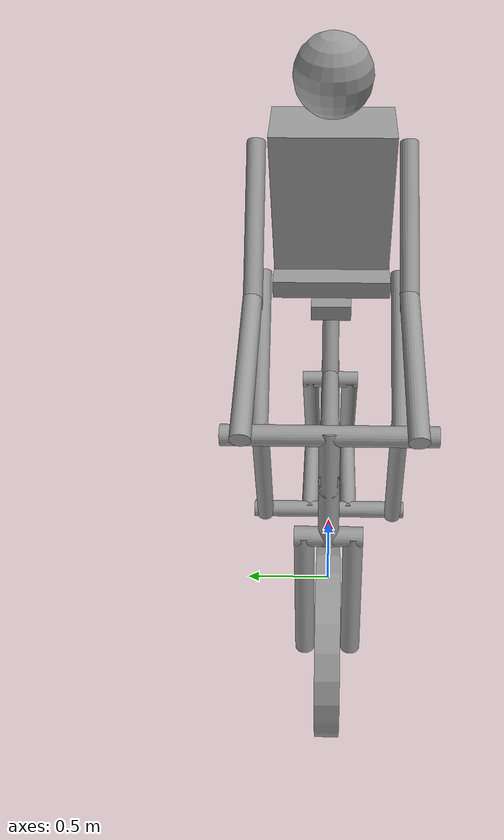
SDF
<?xml version='1.0'?>
<sdf version='1.6'>
  <model name='c_cycle'>
    <link name='link_0'>
      <pose frame=''>1.02325 0 0.352338 1.5707 -0 0</pose>
      <inertial>
        <mass>1</mass>
        <inertia>
          <ixx>0.145833</ixx>
          <ixy>0</ixy>
          <ixz>0</ixz>
          <iyy>0.145833</iyy>
          <iyz>0</iyz>
          <izz>0.125</izz>
        </inertia>
        <pose frame=''>0 0 0 0 -0 0</pose>
      </inertial>
      <self_collide>0</self_collide>
      <kinematic>0</kinematic>
      <visual name='visual'>
        <pose frame=''>0 0 0 0 -0 0</pose>
        <geometry>
          <cylinder>
            <radius>0.5</radius>
            <length>0.12</length>
          </cylinder>
        </geometry>
        <material>
          <lighting>1</lighting>
          <script>
            <uri>file://media/materials/scripts/gazebo.material</uri>
            <name>Gazebo/Grey</name>
          </script>
          <ambient>0.3 0.3 0.3 1</ambient>
          <diffuse>0.7 0.7 0.7 1</diffuse>
          <specular>0.01 0.01 0.01 1</specular>
          <emissive>0 0 0 1</emissive>
          <shader type='vertex'>
            <normal_map>__default__</normal_map>
          </shader>
        </material>
        <cast_shadows>1</cast_shadows>
        <transparency>0</transparency>
      </visual>
      <collision name='collision'>
        <laser_retro>0</laser_retro>
        <max_contacts>10</max_contacts>
        <pose frame=''>0 0 0 0 -0 0</pose>
        <geometry>
          <cylinder>
            <radius>0.5</radius>
            <length>0.12</length>
          </cylinder>
        </geometry>
        <surface>
          <friction>
            <ode>
              <mu>1</mu>
              <mu2>1</mu2>
              <fdir1>0 0 0</fdir1>
              <slip1>0</slip1>
              <slip2>0</slip2>
            </ode>
            <torsional>
              <coefficient>1</coefficient>
              <patch_radius>0</patch_radius>
              <surface_radius>0</surface_radius>
              <use_patch_radius>1</use_patch_radius>
              <ode>
                <slip>0</slip>
              </ode>
            </torsional>
          </friction>
          <bounce>
            <restitution_coefficient>0</restitution_coefficient>
            <threshold>1e+06</threshold>
          </bounce>
          <contact>
            <collide_without_contact>0</collide_without_contact>
            <collide_without_contact_bitmask>1</collide_without_contact_bitmask>
            <collide_bitmask>1</collide_bitmask>
            <ode>
              <soft_cfm>0</soft_cfm>
              <soft_erp>0.2</soft_erp>
              <kp>1e+13</kp>
              <kd>1</kd>
              <max_vel>0.01</max_vel>
              <min_depth>0</min_depth>
            </ode>
            <bullet>
              <split_impulse>1</split_impulse>
              <split_impulse_penetration_threshold>-0.01</split_impulse_penetration_threshold>
              <soft_cfm>0</soft_cfm>
              <soft_erp>0.2</soft_erp>
              <kp>1e+13</kp>
              <kd>1</kd>
            </bullet>
          </contact>
        </surface>
      </collision>
    </link>
    <link name='link_0_0'>
      <pose frame=''>-0.625228 -0.12 0.648148 0 0.169207 0</pose>
      <inertial>
        <mass>0.0814675</mass>
        <inertia>
          <ixx>0.00720375</ixx>
          <ixy>0</ixy>
          <ixz>0</ixz>
          <iyy>0.00720375</iyy>
          <iyz>0</iyz>
          <izz>0.00082962</izz>
        </inertia>
        <pose frame=''>0 0 0 0 -0 0</pose>
      </inertial>
      <self_collide>0</self_collide>
      <kinematic>0</kinematic>
      <visual name='visual'>
        <pose frame=''>0 0 0 0 -0 0</pose>
        <geometry>
          <cylinder>
            <radius>0.05</radius>
            <length>0.75</length>
          </cylinder>
        </geometry>
        <material>
          <lighting>1</lighting>
          <script>
            <uri>file://media/materials/scripts/gazebo.material</uri>
            <name>Gazebo/Grey</name>
          </script>
          <ambient>0.3 0.3 0.3 1</ambient>
          <diffuse>0.7 0.7 0.7 1</diffuse>
          <specular>0.01 0.01 0.01 1</specular>
          <emissive>0 0 0 1</emissive>
          <shader type='vertex'>
            <normal_map>__default__</normal_map>
          </shader>
        </material>
        <cast_shadows>1</cast_shadows>
        <transparency>0</transparency>
      </visual>
      <collision name='collision'>
        <laser_retro>0</laser_retro>
        <max_contacts>10</max_contacts>
        <pose frame=''>0 0 0 0 -0 0</pose>
        <geometry>
          <cylinder>
            <radius>0.05</radius>
            <length>0.75</length>
          </cylinder>
        </geometry>
        <surface>
          <friction>
            <ode>
              <mu>1</mu>
              <mu2>1</mu2>
              <fdir1>0 0 0</fdir1>
              <slip1>0</slip1>
              <slip2>0</slip2>
            </ode>
            <torsional>
              <coefficient>1</coefficient>
              <patch_radius>0</patch_radius>
              <surface_radius>0</surface_radius>
              <use_patch_radius>1</use_patch_radius>
              <ode>
                <slip>0</slip>
              </ode>
            </torsional>
          </friction>
          <bounce>
            <restitution_coefficient>0</restitution_coefficient>
            <threshold>1e+06</threshold>
          </bounce>
          <contact>
            <collide_without_contact>0</collide_without_contact>
            <collide_without_contact_bitmask>1</collide_without_contact_bitmask>
            <collide_bitmask>1</collide_bitmask>
            <ode>
              <soft_cfm>0</soft_cfm>
              <soft_erp>0.2</soft_erp>
              <kp>1e+13</kp>
              <kd>1</kd>
              <max_vel>0.01</max_vel>
              <min_depth>0</min_depth>
            </ode>
            <bullet>
              <split_impulse>1</split_impulse>
              <split_impulse_penetration_threshold>-0.01</split_impulse_penetration_threshold>
              <soft_cfm>0</soft_cfm>
              <soft_erp>0.2</soft_erp>
              <kp>1e+13</kp>
              <kd>1</kd>
            </bullet>
          </contact>
        </surface>
      </collision>
    </link>
    <link name='link_0_0_clone'>
      <pose frame=''>-0.625228 0.12 0.648148 0 0.169207 0</pose>
      <inertial>
        <mass>0.0814675</mass>
        <inertia>
          <ixx>0.00720375</ixx>
          <ixy>0</ixy>
          <ixz>0</ixz>
          <iyy>0.00720375</iyy>
          <iyz>0</iyz>
          <izz>0.00082962</izz>
        </inertia>
        <pose frame=''>0 0 0 0 -0 0</pose>
      </inertial>
      <self_collide>0</self_collide>
      <kinematic>0</kinematic>
      <visual name='visual_0'>
        <pose frame=''>0 0 0 0 -0 0</pose>
        <geometry>
          <cylinder>
            <radius>0.05</radius>
            <length>0.75</length>
          </cylinder>
        </geometry>
        <material>
          <lighting>1</lighting>
          <script>
            <uri>file://media/materials/scripts/gazebo.material</uri>
            <name>Gazebo/Grey</name>
          </script>
          <ambient>0.3 0.3 0.3 1</ambient>
          <diffuse>0.7 0.7 0.7 1</diffuse>
          <specular>0.01 0.01 0.01 1</specular>
          <emissive>0 0 0 1</emissive>
          <shader type='vertex'>
            <normal_map>__default__</normal_map>
          </shader>
        </material>
        <cast_shadows>1</cast_shadows>
        <transparency>0</transparency>
      </visual>
      <collision name='collision'>
        <laser_retro>0</laser_retro>
        <max_contacts>10</max_contacts>
        <pose frame=''>0 0 0 0 -0 0</pose>
        <geometry>
          <cylinder>
            <radius>0.05</radius>
            <length>0.75</length>
          </cylinder>
        </geometry>
        <surface>
          <friction>
            <ode>
              <mu>1</mu>
              <mu2>1</mu2>
              <fdir1>0 0 0</fdir1>
              <slip1>0</slip1>
              <slip2>0</slip2>
            </ode>
            <torsional>
              <coefficient>1</coefficient>
              <patch_radius>0</patch_radius>
              <surface_radius>0</surface_radius>
              <use_patch_radius>1</use_patch_radius>
              <ode>
                <slip>0</slip>
              </ode>
            </torsional>
          </friction>
          <bounce>
            <restitution_coefficient>0</restitution_coefficient>
            <threshold>1e+06</threshold>
          </bounce>
          <contact>
            <collide_without_contact>0</collide_without_contact>
            <collide_without_contact_bitmask>1</collide_without_contact_bitmask>
            <collide_bitmask>1</collide_bitmask>
            <ode>
              <soft_cfm>0</soft_cfm>
              <soft_erp>0.2</soft_erp>
              <kp>1e+13</kp>
              <kd>1</kd>
              <max_vel>0.01</max_vel>
              <min_depth>0</min_depth>
            </ode>
            <bullet>
              <split_impulse>1</split_impulse>
              <split_impulse_penetration_threshold>-0.01</split_impulse_penetration_threshold>
              <soft_cfm>0</soft_cfm>
              <soft_erp>0.2</soft_erp>
              <kp>1e+13</kp>
              <kd>1</kd>
            </bullet>
          </contact>
        </surface>
      </collision>
    </link>
    <link name='link_0_1'>
      <pose frame=''>0.891331 -0 2.17231 -0.000132 -0.132222 0.001101</pose>
      <inertial>
        <mass>0.178724</mass>
        <inertia>
          <ixx>0.0153559</ixx>
          <ixy>0</ixy>
          <ixz>0</ixz>
          <iyy>0.0109514</iyy>
          <iyz>0</iyz>
          <izz>0.00811157</izz>
        </inertia>
        <pose frame=''>0 0 0 0 -0 0</pose>
      </inertial>
      <self_collide>0</self_collide>
      <kinematic>0</kinematic>
      <visual name='visual'>
        <pose frame=''>0 0 0 0 -0 0</pose>
        <geometry>
          <box>
            <size>0.352777 0.648218 0.781572</size>
          </box>
        </geometry>
        <material>
          <lighting>1</lighting>
          <script>
            <uri>file://media/materials/scripts/gazebo.material</uri>
            <name>Gazebo/Grey</name>
          </script>
          <ambient>0.3 0.3 0.3 1</ambient>
          <diffuse>0.7 0.7 0.7 1</diffuse>
          <specular>0.01 0.01 0.01 1</specular>
          <emissive>0 0 0 1</emissive>
          <shader type='vertex'>
            <normal_map>__default__</normal_map>
          </shader>
        </material>
        <cast_shadows>1</cast_shadows>
        <transparency>0</transparency>
      </visual>
      <collision name='collision'>
        <laser_retro>0</laser_retro>
        <max_contacts>10</max_contacts>
        <pose frame=''>0 0 0 0 -0 0</pose>
        <geometry>
          <box>
            <size>0.352777 0.648218 0.781572</size>
          </box>
        </geometry>
        <surface>
          <friction>
            <ode>
              <mu>1</mu>
              <mu2>1</mu2>
              <fdir1>0 0 0</fdir1>
              <slip1>0</slip1>
              <slip2>0</slip2>
            </ode>
            <torsional>
              <coefficient>1</coefficient>
              <patch_radius>0</patch_radius>
              <surface_radius>0</surface_radius>
              <use_patch_radius>1</use_patch_radius>
              <ode>
                <slip>0</slip>
              </ode>
            </torsional>
          </friction>
          <bounce>
            <restitution_coefficient>0</restitution_coefficient>
            <threshold>1e+06</threshold>
          </bounce>
          <contact>
            <collide_without_contact>0</collide_without_contact>
            <collide_without_contact_bitmask>1</collide_without_contact_bitmask>
            <collide_bitmask>1</collide_bitmask>
            <ode>
              <soft_cfm>0</soft_cfm>
              <soft_erp>0.2</soft_erp>
              <kp>1e+13</kp>
              <kd>1</kd>
              <max_vel>0.01</max_vel>
              <min_depth>0</min_depth>
            </ode>
            <bullet>
              <split_impulse>1</split_impulse>
              <split_impulse_penetration_threshold>-0.01</split_impulse_penetration_threshold>
              <soft_cfm>0</soft_cfm>
              <soft_erp>0.2</soft_erp>
              <kp>1e+13</kp>
              <kd>1</kd>
            </bullet>
          </contact>
        </surface>
      </collision>
    </link>
    <link name='link_0_clone'>
      <pose frame=''>-0.669823 -0 0.352338 1.5707 -0 0</pose>
      <inertial>
        <mass>1</mass>
        <inertia>
          <ixx>0.145833</ixx>
          <ixy>0</ixy>
          <ixz>0</ixz>
          <iyy>0.145833</iyy>
          <iyz>0</iyz>
          <izz>0.125</izz>
        </inertia>
        <pose frame=''>0 0 0 0 -0 0</pose>
      </inertial>
      <self_collide>0</self_collide>
      <kinematic>0</kinematic>
      <visual name='visual'>
        <pose frame=''>0 0 0 0 -0 0</pose>
        <geometry>
          <cylinder>
            <radius>0.5</radius>
            <length>0.12</length>
          </cylinder>
        </geometry>
        <material>
          <lighting>1</lighting>
          <script>
            <uri>file://media/materials/scripts/gazebo.material</uri>
            <name>Gazebo/Grey</name>
          </script>
          <ambient>0.3 0.3 0.3 1</ambient>
          <diffuse>0.7 0.7 0.7 1</diffuse>
          <specular>0.01 0.01 0.01 1</specular>
          <emissive>0 0 0 1</emissive>
          <shader type='vertex'>
            <normal_map>__default__</normal_map>
          </shader>
        </material>
        <cast_shadows>1</cast_shadows>
        <transparency>0</transparency>
      </visual>
      <collision name='collision'>
        <laser_retro>0</laser_retro>
        <max_contacts>10</max_contacts>
        <pose frame=''>0 0 0 0 -0 0</pose>
        <geometry>
          <cylinder>
            <radius>0.5</radius>
            <length>0.12</length>
          </cylinder>
        </geometry>
        <surface>
          <friction>
            <ode>
              <mu>1</mu>
              <mu2>1</mu2>
              <fdir1>0 0 0</fdir1>
              <slip1>0</slip1>
              <slip2>0</slip2>
            </ode>
            <torsional>
              <coefficient>1</coefficient>
              <patch_radius>0</patch_radius>
              <surface_radius>0</surface_radius>
              <use_patch_radius>1</use_patch_radius>
              <ode>
                <slip>0</slip>
              </ode>
            </torsional>
          </friction>
          <bounce>
            <restitution_coefficient>0</restitution_coefficient>
            <threshold>1e+06</threshold>
          </bounce>
          <contact>
            <collide_without_contact>0</collide_without_contact>
            <collide_without_contact_bitmask>1</collide_without_contact_bitmask>
            <collide_bitmask>1</collide_bitmask>
            <ode>
              <soft_cfm>0</soft_cfm>
              <soft_erp>0.2</soft_erp>
              <kp>1e+13</kp>
              <kd>1</kd>
              <max_vel>0.01</max_vel>
              <min_depth>0</min_depth>
            </ode>
            <bullet>
              <split_impulse>1</split_impulse>
              <split_impulse_penetration_threshold>-0.01</split_impulse_penetration_threshold>
              <soft_cfm>0</soft_cfm>
              <soft_erp>0.2</soft_erp>
              <kp>1e+13</kp>
              <kd>1</kd>
            </bullet>
          </contact>
        </surface>
      </collision>
    </link>
    <link name='link_1'>
      <pose frame=''>-0.51299 0 1.28445 0 0.187784 0</pose>
      <inertial>
        <mass>0.778608</mass>
        <inertia>
          <ixx>0.0879975</ixx>
          <ixy>0</ixy>
          <ixz>0</ixz>
          <iyy>0.0879975</iyy>
          <iyz>0</iyz>
          <izz>0.097326</izz>
        </inertia>
        <pose frame=''>0 0 0 0 -0 0</pose>
      </inertial>
      <self_collide>0</self_collide>
      <kinematic>0</kinematic>
      <visual name='visual'>
        <pose frame=''>0 0 0 0 -0 0</pose>
        <geometry>
          <cylinder>
            <radius>0.05</radius>
            <length>0.622887</length>
          </cylinder>
        </geometry>
        <material>
          <lighting>1</lighting>
          <script>
            <uri>file://media/materials/scripts/gazebo.material</uri>
            <name>Gazebo/Grey</name>
          </script>
          <ambient>0.3 0.3 0.3 1</ambient>
          <diffuse>0.7 0.7 0.7 1</diffuse>
          <specular>0.01 0.01 0.01 1</specular>
          <emissive>0 0 0 1</emissive>
          <shader type='vertex'>
            <normal_map>__default__</normal_map>
          </shader>
        </material>
        <cast_shadows>1</cast_shadows>
        <transparency>0</transparency>
      </visual>
      <collision name='collision'>
        <laser_retro>0</laser_retro>
        <max_contacts>10</max_contacts>
        <pose frame=''>0 0 0 0 -0 0</pose>
        <geometry>
          <cylinder>
            <radius>0.05</radius>
            <length>0.622887</length>
          </cylinder>
        </geometry>
        <surface>
          <friction>
            <ode>
              <mu>1</mu>
              <mu2>1</mu2>
              <fdir1>0 0 0</fdir1>
              <slip1>0</slip1>
              <slip2>0</slip2>
            </ode>
            <torsional>
              <coefficient>1</coefficient>
              <patch_radius>0</patch_radius>
              <surface_radius>0</surface_radius>
              <use_patch_radius>1</use_patch_radius>
              <ode>
                <slip>0</slip>
              </ode>
            </torsional>
          </friction>
          <bounce>
            <restitution_coefficient>0</restitution_coefficient>
            <threshold>1e+06</threshold>
          </bounce>
          <contact>
            <collide_without_contact>0</collide_without_contact>
            <collide_without_contact_bitmask>1</collide_without_contact_bitmask>
            <collide_bitmask>1</collide_bitmask>
            <ode>
              <soft_cfm>0</soft_cfm>
              <soft_erp>0.2</soft_erp>
              <kp>1e+13</kp>
              <kd>1</kd>
              <max_vel>0.01</max_vel>
              <min_depth>0</min_depth>
            </ode>
            <bullet>
              <split_impulse>1</split_impulse>
              <split_impulse_penetration_threshold>-0.01</split_impulse_penetration_threshold>
              <soft_cfm>0</soft_cfm>
              <soft_erp>0.2</soft_erp>
              <kp>1e+13</kp>
              <kd>1</kd>
            </bullet>
          </contact>
        </surface>
      </collision>
    </link>
    <link name='link_1_0'>
      <pose frame=''>0.820607 -0 2.78662 -0.000134 -0.222442 0.001114</pose>
      <inertial>
        <mass>0.0659506</mass>
        <inertia>
          <ixx>0.00107654</ixx>
          <ixy>0</ixy>
          <ixz>0</ixz>
          <iyy>0.00107654</iyy>
          <iyz>0</iyz>
          <izz>0.00107654</izz>
        </inertia>
        <pose frame=''>0 0 0 0 -0 0</pose>
      </inertial>
      <self_collide>0</self_collide>
      <kinematic>0</kinematic>
      <visual name='visual'>
        <pose frame=''>0 0 0 0 -0 0</pose>
        <geometry>
          <sphere>
            <radius>0.202012</radius>
          </sphere>
        </geometry>
        <material>
          <lighting>1</lighting>
          <script>
            <uri>file://media/materials/scripts/gazebo.material</uri>
            <name>Gazebo/Grey</name>
          </script>
          <ambient>0.3 0.3 0.3 1</ambient>
          <diffuse>0.7 0.7 0.7 1</diffuse>
          <specular>0.01 0.01 0.01 1</specular>
          <emissive>0 0 0 1</emissive>
          <shader type='vertex'>
            <normal_map>__default__</normal_map>
          </shader>
        </material>
        <cast_shadows>1</cast_shadows>
        <transparency>0</transparency>
      </visual>
      <collision name='collision'>
        <laser_retro>0</laser_retro>
        <max_contacts>10</max_contacts>
        <pose frame=''>0 0 0 0 -0 0</pose>
        <geometry>
          <sphere>
            <radius>0.202012</radius>
          </sphere>
        </geometry>
        <surface>
          <friction>
            <ode>
              <mu>1</mu>
              <mu2>1</mu2>
              <fdir1>0 0 0</fdir1>
              <slip1>0</slip1>
              <slip2>0</slip2>
            </ode>
            <torsional>
              <coefficient>1</coefficient>
              <patch_radius>0</patch_radius>
              <surface_radius>0</surface_radius>
              <use_patch_radius>1</use_patch_radius>
              <ode>
                <slip>0</slip>
              </ode>
            </torsional>
          </friction>
          <bounce>
            <restitution_coefficient>0</restitution_coefficient>
            <threshold>1e+06</threshold>
          </bounce>
          <contact>
            <collide_without_contact>0</collide_without_contact>
            <collide_without_contact_bitmask>1</collide_without_contact_bitmask>
            <collide_bitmask>1</collide_bitmask>
            <ode>
              <soft_cfm>0</soft_cfm>
              <soft_erp>0.2</soft_erp>
              <kp>1e+13</kp>
              <kd>1</kd>
              <max_vel>0.01</max_vel>
              <min_depth>0</min_depth>
            </ode>
            <bullet>
              <split_impulse>1</split_impulse>
              <split_impulse_penetration_threshold>-0.01</split_impulse_penetration_threshold>
              <soft_cfm>0</soft_cfm>
              <soft_erp>0.2</soft_erp>
              <kp>1e+13</kp>
              <kd>1</kd>
            </bullet>
          </contact>
        </surface>
      </collision>
    </link>
    <link name='link_2'>
      <pose frame=''>0.613954 0.12 0.352338 -4e-06 -1.5707 4e-06</pose>
      <inertial>
        <mass>1</mass>
        <inertia>
          <ixx>0.145833</ixx>
          <ixy>0</ixy>
          <ixz>0</ixz>
          <iyy>0.145833</iyy>
          <iyz>0</iyz>
          <izz>0.125</izz>
        </inertia>
        <pose frame=''>0 0 0 0 -0 0</pose>
      </inertial>
      <self_collide>0</self_collide>
      <kinematic>0</kinematic>
      <visual name='visual'>
        <pose frame=''>0 0 0 0 -0 0</pose>
        <geometry>
          <cylinder>
            <radius>0.05</radius>
            <length>0.75</length>
          </cylinder>
        </geometry>
        <material>
          <lighting>1</lighting>
          <script>
            <uri>file://media/materials/scripts/gazebo.material</uri>
            <name>Gazebo/Grey</name>
          </script>
          <ambient>0.3 0.3 0.3 1</ambient>
          <diffuse>0.7 0.7 0.7 1</diffuse>
          <specular>0.01 0.01 0.01 1</specular>
          <emissive>0 0 0 1</emissive>
          <shader type='vertex'>
            <normal_map>__default__</normal_map>
          </shader>
        </material>
        <cast_shadows>1</cast_shadows>
        <transparency>0</transparency>
      </visual>
      <collision name='collision'>
        <laser_retro>0</laser_retro>
        <max_contacts>10</max_contacts>
        <pose frame=''>0 0 0 0 -0 0</pose>
        <geometry>
          <cylinder>
            <radius>0.05</radius>
            <length>0.75</length>
          </cylinder>
        </geometry>
        <surface>
          <friction>
            <ode>
              <mu>1</mu>
              <mu2>1</mu2>
              <fdir1>0 0 0</fdir1>
              <slip1>0</slip1>
              <slip2>0</slip2>
            </ode>
            <torsional>
              <coefficient>1</coefficient>
              <patch_radius>0</patch_radius>
              <surface_radius>0</surface_radius>
              <use_patch_radius>1</use_patch_radius>
              <ode>
                <slip>0</slip>
              </ode>
            </torsional>
          </friction>
          <bounce>
            <restitution_coefficient>0</restitution_coefficient>
            <threshold>1e+06</threshold>
          </bounce>
          <contact>
            <collide_without_contact>0</collide_without_contact>
            <collide_without_contact_bitmask>1</collide_without_contact_bitmask>
            <collide_bitmask>1</collide_bitmask>
            <ode>
              <soft_cfm>0</soft_cfm>
              <soft_erp>0.2</soft_erp>
              <kp>1e+13</kp>
              <kd>1</kd>
              <max_vel>0.01</max_vel>
              <min_depth>0</min_depth>
            </ode>
            <bullet>
              <split_impulse>1</split_impulse>
              <split_impulse_penetration_threshold>-0.01</split_impulse_penetration_threshold>
              <soft_cfm>0</soft_cfm>
              <soft_erp>0.2</soft_erp>
              <kp>1e+13</kp>
              <kd>1</kd>
            </bullet>
          </contact>
        </surface>
      </collision>
    </link>
    <link name='link_2_0'>
      <pose frame=''>0.080962 0 1.21125 0 -1.3588 0</pose>
      <inertial>
        <mass>1.25519</mass>
        <inertia>
          <ixx>0.243245</ixx>
          <ixy>0</ixy>
          <ixz>0</ixz>
          <iyy>0.243245</iyy>
          <iyz>0</iyz>
          <izz>0.156899</izz>
        </inertia>
        <pose frame=''>0 0 0 0 -0 0</pose>
      </inertial>
      <self_collide>0</self_collide>
      <kinematic>0</kinematic>
      <visual name='visual'>
        <pose frame=''>0 0 0 0 -0 0</pose>
        <geometry>
          <cylinder>
            <radius>0.05</radius>
            <length>1.25519</length>
          </cylinder>
        </geometry>
        <material>
          <lighting>1</lighting>
          <script>
            <uri>file://media/materials/scripts/gazebo.material</uri>
            <name>Gazebo/Grey</name>
          </script>
          <ambient>0.3 0.3 0.3 1</ambient>
          <diffuse>0.7 0.7 0.7 1</diffuse>
          <specular>0.01 0.01 0.01 1</specular>
          <emissive>0 0 0 1</emissive>
          <shader type='vertex'>
            <normal_map>__default__</normal_map>
          </shader>
        </material>
        <cast_shadows>1</cast_shadows>
        <transparency>0</transparency>
      </visual>
      <collision name='collision'>
        <laser_retro>0</laser_retro>
        <max_contacts>10</max_contacts>
        <pose frame=''>0 0 0 0 -0 0</pose>
        <geometry>
          <cylinder>
            <radius>0.05</radius>
            <length>1.25519</length>
          </cylinder>
        </geometry>
        <surface>
          <friction>
            <ode>
              <mu>1</mu>
              <mu2>1</mu2>
              <fdir1>0 0 0</fdir1>
              <slip1>0</slip1>
              <slip2>0</slip2>
            </ode>
            <torsional>
              <coefficient>1</coefficient>
              <patch_radius>0</patch_radius>
              <surface_radius>0</surface_radius>
              <use_patch_radius>1</use_patch_radius>
              <ode>
                <slip>0</slip>
              </ode>
            </torsional>
          </friction>
          <bounce>
            <restitution_coefficient>0</restitution_coefficient>
            <threshold>1e+06</threshold>
          </bounce>
          <contact>
            <collide_without_contact>0</collide_without_contact>
            <collide_without_contact_bitmask>1</collide_without_contact_bitmask>
            <collide_bitmask>1</collide_bitmask>
            <ode>
              <soft_cfm>0</soft_cfm>
              <soft_erp>0.2</soft_erp>
              <kp>1e+13</kp>
              <kd>1</kd>
              <max_vel>0.01</max_vel>
              <min_depth>0</min_depth>
            </ode>
            <bullet>
              <split_impulse>1</split_impulse>
              <split_impulse_penetration_threshold>-0.01</split_impulse_penetration_threshold>
              <soft_cfm>0</soft_cfm>
              <soft_erp>0.2</soft_erp>
              <kp>1e+13</kp>
              <kd>1</kd>
            </bullet>
          </contact>
        </surface>
      </collision>
    </link>
    <link name='link_2_0_clone'>
      <pose frame=''>-0.112381 0.400249 1.72995 -3.14114 -1.27847 -3.14094</pose>
      <inertial>
        <mass>0.89557</mass>
        <inertia>
          <ixx>0.11583</ixx>
          <ixy>0</ixy>
          <ixz>0</ixz>
          <iyy>0.11583</iyy>
          <iyz>0</iyz>
          <izz>0.111946</izz>
        </inertia>
        <pose frame=''>0 0 0 0 -0 0</pose>
      </inertial>
      <self_collide>0</self_collide>
      <kinematic>0</kinematic>
      <visual name='visual'>
        <pose frame=''>0 0 0 0 -0 0</pose>
        <geometry>
          <cylinder>
            <radius>0.05</radius>
            <length>0.89557</length>
          </cylinder>
        </geometry>
        <material>
          <lighting>1</lighting>
          <script>
            <uri>file://media/materials/scripts/gazebo.material</uri>
            <name>Gazebo/Grey</name>
          </script>
          <ambient>0.3 0.3 0.3 1</ambient>
          <diffuse>0.7 0.7 0.7 1</diffuse>
          <specular>0.01 0.01 0.01 1</specular>
          <emissive>0 0 0 1</emissive>
          <shader type='vertex'>
            <normal_map>__default__</normal_map>
          </shader>
        </material>
        <cast_shadows>1</cast_shadows>
        <transparency>0</transparency>
      </visual>
      <collision name='collision'>
        <laser_retro>0</laser_retro>
        <max_contacts>10</max_contacts>
        <pose frame=''>0 0 0 0 -0 0</pose>
        <geometry>
          <cylinder>
            <radius>0.05</radius>
            <length>0.89557</length>
          </cylinder>
        </geometry>
        <surface>
          <friction>
            <ode>
              <mu>1</mu>
              <mu2>1</mu2>
              <fdir1>0 0 0</fdir1>
              <slip1>0</slip1>
              <slip2>0</slip2>
            </ode>
            <torsional>
              <coefficient>1</coefficient>
              <patch_radius>0</patch_radius>
              <surface_radius>0</surface_radius>
              <use_patch_radius>1</use_patch_radius>
              <ode>
                <slip>0</slip>
              </ode>
            </torsional>
          </friction>
          <bounce>
            <restitution_coefficient>0</restitution_coefficient>
            <threshold>1e+06</threshold>
          </bounce>
          <contact>
            <collide_without_contact>0</collide_without_contact>
            <collide_without_contact_bitmask>1</collide_without_contact_bitmask>
            <collide_bitmask>1</collide_bitmask>
            <ode>
              <soft_cfm>0</soft_cfm>
              <soft_erp>0.2</soft_erp>
              <kp>1e+13</kp>
              <kd>1</kd>
              <max_vel>0.01</max_vel>
              <min_depth>0</min_depth>
            </ode>
            <bullet>
              <split_impulse>1</split_impulse>
              <split_impulse_penetration_threshold>-0.01</split_impulse_penetration_threshold>
              <soft_cfm>0</soft_cfm>
              <soft_erp>0.2</soft_erp>
              <kp>1e+13</kp>
              <kd>1</kd>
            </bullet>
          </contact>
        </surface>
      </collision>
    </link>
    <link name='link_2_0_clone_clone'>
      <pose frame=''>-0.112381 -0.400249 1.72995 -3.14067 -1.25604 -3.1403</pose>
      <inertial>
        <mass>0.89557</mass>
        <inertia>
          <ixx>0.11583</ixx>
          <ixy>0</ixy>
          <ixz>0</ixz>
          <iyy>0.11583</iyy>
          <iyz>0</iyz>
          <izz>0.111946</izz>
        </inertia>
        <pose frame=''>0 0 0 0 -0 0</pose>
      </inertial>
      <self_collide>0</self_collide>
      <kinematic>0</kinematic>
      <visual name='visual'>
        <pose frame=''>0 0 0 0 -0 0</pose>
        <geometry>
          <cylinder>
            <radius>0.05</radius>
            <length>0.89557</length>
          </cylinder>
        </geometry>
        <material>
          <lighting>1</lighting>
          <script>
            <uri>file://media/materials/scripts/gazebo.material</uri>
            <name>Gazebo/Grey</name>
          </script>
          <ambient>0.3 0.3 0.3 1</ambient>
          <diffuse>0.7 0.7 0.7 1</diffuse>
          <specular>0.01 0.01 0.01 1</specular>
          <emissive>0 0 0 1</emissive>
          <shader type='vertex'>
            <normal_map>__default__</normal_map>
          </shader>
        </material>
        <cast_shadows>1</cast_shadows>
        <transparency>0</transparency>
      </visual>
      <collision name='collision'>
        <laser_retro>0</laser_retro>
        <max_contacts>10</max_contacts>
        <pose frame=''>0 0 0 0 -0 0</pose>
        <geometry>
          <cylinder>
            <radius>0.05</radius>
            <length>0.89557</length>
          </cylinder>
        </geometry>
        <surface>
          <friction>
            <ode>
              <mu>1</mu>
              <mu2>1</mu2>
              <fdir1>0 0 0</fdir1>
              <slip1>0</slip1>
              <slip2>0</slip2>
            </ode>
            <torsional>
              <coefficient>1</coefficient>
              <patch_radius>0</patch_radius>
              <surface_radius>0</surface_radius>
              <use_patch_radius>1</use_patch_radius>
              <ode>
                <slip>0</slip>
              </ode>
            </torsional>
          </friction>
          <bounce>
            <restitution_coefficient>0</restitution_coefficient>
            <threshold>1e+06</threshold>
          </bounce>
          <contact>
            <collide_without_contact>0</collide_without_contact>
            <collide_without_contact_bitmask>1</collide_without_contact_bitmask>
            <collide_bitmask>1</collide_bitmask>
            <ode>
              <soft_cfm>0</soft_cfm>
              <soft_erp>0.2</soft_erp>
              <kp>1e+13</kp>
              <kd>1</kd>
              <max_vel>0.01</max_vel>
              <min_depth>0</min_depth>
            </ode>
            <bullet>
              <split_impulse>1</split_impulse>
              <split_impulse_penetration_threshold>-0.01</split_impulse_penetration_threshold>
              <soft_cfm>0</soft_cfm>
              <soft_erp>0.2</soft_erp>
              <kp>1e+13</kp>
              <kd>1</kd>
            </bullet>
          </contact>
        </surface>
      </collision>
    </link>
    <link name='link_2_1'>
      <pose frame=''>0.558223 -0.4 2.1264 -0.000404 0.784195 0.00188</pose>
      <inertial>
        <mass>1</mass>
        <inertia>
          <ixx>0.145833</ixx>
          <ixy>0</ixy>
          <ixz>0</ixz>
          <iyy>0.145833</iyy>
          <iyz>0</iyz>
          <izz>0.125</izz>
        </inertia>
        <pose frame=''>0 0 0 0 -0 0</pose>
      </inertial>
      <self_collide>0</self_collide>
      <kinematic>0</kinematic>
      <visual name='visual'>
        <pose frame=''>0 0 0 0 -0 0</pose>
        <geometry>
          <cylinder>
            <radius>0.05</radius>
            <length>0.896706</length>
          </cylinder>
        </geometry>
        <material>
          <lighting>1</lighting>
          <script>
            <uri>file://media/materials/scripts/gazebo.material</uri>
            <name>Gazebo/Grey</name>
          </script>
          <ambient>0.3 0.3 0.3 1</ambient>
          <diffuse>0.7 0.7 0.7 1</diffuse>
          <specular>0.01 0.01 0.01 1</specular>
          <emissive>0 0 0 1</emissive>
          <shader type='vertex'>
            <normal_map>__default__</normal_map>
          </shader>
        </material>
        <cast_shadows>1</cast_shadows>
        <transparency>0</transparency>
      </visual>
      <collision name='collision'>
        <laser_retro>0</laser_retro>
        <max_contacts>10</max_contacts>
        <pose frame=''>0 0 0 0 -0 0</pose>
        <geometry>
          <cylinder>
            <radius>0.05</radius>
            <length>0.896706</length>
          </cylinder>
        </geometry>
        <surface>
          <friction>
            <ode>
              <mu>1</mu>
              <mu2>1</mu2>
              <fdir1>0 0 0</fdir1>
              <slip1>0</slip1>
              <slip2>0</slip2>
            </ode>
            <torsional>
              <coefficient>1</coefficient>
              <patch_radius>0</patch_radius>
              <surface_radius>0</surface_radius>
              <use_patch_radius>1</use_patch_radius>
              <ode>
                <slip>0</slip>
              </ode>
            </torsional>
          </friction>
          <bounce>
            <restitution_coefficient>0</restitution_coefficient>
            <threshold>1e+06</threshold>
          </bounce>
          <contact>
            <collide_without_contact>0</collide_without_contact>
            <collide_without_contact_bitmask>1</collide_without_contact_bitmask>
            <collide_bitmask>1</collide_bitmask>
            <ode>
              <soft_cfm>0</soft_cfm>
              <soft_erp>0.2</soft_erp>
              <kp>1e+13</kp>
              <kd>1</kd>
              <max_vel>0.01</max_vel>
              <min_depth>0</min_depth>
            </ode>
            <bullet>
              <split_impulse>1</split_impulse>
              <split_impulse_penetration_threshold>-0.01</split_impulse_penetration_threshold>
              <soft_cfm>0</soft_cfm>
              <soft_erp>0.2</soft_erp>
              <kp>1e+13</kp>
              <kd>1</kd>
            </bullet>
          </contact>
        </surface>
      </collision>
    </link>
    <link name='link_2_1_clone'>
      <pose frame=''>0.558223 0.4 2.1264 -0.000404 0.784195 0.00188</pose>
      <inertial>
        <mass>0.896706</mass>
        <inertia>
          <ixx>0.116129</ixx>
          <ixy>0</ixy>
          <ixz>0</ixz>
          <iyy>0.116129</iyy>
          <iyz>0</iyz>
          <izz>0.112088</izz>
        </inertia>
        <pose frame=''>0 0 0 0 -0 0</pose>
      </inertial>
      <self_collide>0</self_collide>
      <kinematic>0</kinematic>
      <visual name='visual_0'>
        <pose frame=''>0 0 0 0 -0 0</pose>
        <geometry>
          <cylinder>
            <radius>0.05</radius>
            <length>0.896706</length>
          </cylinder>
        </geometry>
        <material>
          <lighting>1</lighting>
          <script>
            <uri>file://media/materials/scripts/gazebo.material</uri>
            <name>Gazebo/Grey</name>
          </script>
          <ambient>0.3 0.3 0.3 1</ambient>
          <diffuse>0.7 0.7 0.7 1</diffuse>
          <specular>0.01 0.01 0.01 1</specular>
          <emissive>0 0 0 1</emissive>
          <shader type='vertex'>
            <normal_map>__default__</normal_map>
          </shader>
        </material>
        <cast_shadows>1</cast_shadows>
        <transparency>0</transparency>
      </visual>
      <collision name='collision'>
        <laser_retro>0</laser_retro>
        <max_contacts>10</max_contacts>
        <pose frame=''>0 0 0 0 -0 0</pose>
        <geometry>
          <cylinder>
            <radius>0.05</radius>
            <length>0.896706</length>
          </cylinder>
        </geometry>
        <surface>
          <friction>
            <ode>
              <mu>1</mu>
              <mu2>1</mu2>
              <fdir1>0 0 0</fdir1>
              <slip1>0</slip1>
              <slip2>0</slip2>
            </ode>
            <torsional>
              <coefficient>1</coefficient>
              <patch_radius>0</patch_radius>
              <surface_radius>0</surface_radius>
              <use_patch_radius>1</use_patch_radius>
              <ode>
                <slip>0</slip>
              </ode>
            </torsional>
          </friction>
          <bounce>
            <restitution_coefficient>0</restitution_coefficient>
            <threshold>1e+06</threshold>
          </bounce>
          <contact>
            <collide_without_contact>0</collide_without_contact>
            <collide_without_contact_bitmask>1</collide_without_contact_bitmask>
            <collide_bitmask>1</collide_bitmask>
            <ode>
              <soft_cfm>0</soft_cfm>
              <soft_erp>0.2</soft_erp>
              <kp>1e+13</kp>
              <kd>1</kd>
              <max_vel>0.01</max_vel>
              <min_depth>0</min_depth>
            </ode>
            <bullet>
              <split_impulse>1</split_impulse>
              <split_impulse_penetration_threshold>-0.01</split_impulse_penetration_threshold>
              <soft_cfm>0</soft_cfm>
              <soft_erp>0.2</soft_erp>
              <kp>1e+13</kp>
              <kd>1</kd>
            </bullet>
          </contact>
        </surface>
      </collision>
    </link>
    <link name='link_3'>
      <pose frame=''>-0.126846 0 0.807094 0 -0.683358 0</pose>
      <inertial>
        <mass>1.27165</mass>
        <inertia>
          <ixx>0.250842</ixx>
          <ixy>0</ixy>
          <ixz>0</ixz>
          <iyy>0.250842</iyy>
          <iyz>0</iyz>
          <izz>0.158956</izz>
        </inertia>
        <pose frame=''>0 0 0 0 -0 0</pose>
      </inertial>
      <self_collide>0</self_collide>
      <kinematic>0</kinematic>
      <visual name='visual'>
        <pose frame=''>0 0 0 0 -0 0</pose>
        <geometry>
          <cylinder>
            <radius>0.05</radius>
            <length>1.27165</length>
          </cylinder>
        </geometry>
        <material>
          <lighting>1</lighting>
          <script>
            <uri>file://media/materials/scripts/gazebo.material</uri>
            <name>Gazebo/Grey</name>
          </script>
          <ambient>0.3 0.3 0.3 1</ambient>
          <diffuse>0.7 0.7 0.7 1</diffuse>
          <specular>0.01 0.01 0.01 1</specular>
          <emissive>0 0 0 1</emissive>
          <shader type='vertex'>
            <normal_map>__default__</normal_map>
          </shader>
        </material>
        <cast_shadows>1</cast_shadows>
        <transparency>0</transparency>
      </visual>
      <collision name='collision'>
        <laser_retro>0</laser_retro>
        <max_contacts>10</max_contacts>
        <pose frame=''>0 0 0 0 -0 0</pose>
        <geometry>
          <cylinder>
            <radius>0.05</radius>
            <length>1.27165</length>
          </cylinder>
        </geometry>
        <surface>
          <friction>
            <ode>
              <mu>1</mu>
              <mu2>1</mu2>
              <fdir1>0 0 0</fdir1>
              <slip1>0</slip1>
              <slip2>0</slip2>
            </ode>
            <torsional>
              <coefficient>1</coefficient>
              <patch_radius>0</patch_radius>
              <surface_radius>0</surface_radius>
              <use_patch_radius>1</use_patch_radius>
              <ode>
                <slip>0</slip>
              </ode>
            </torsional>
          </friction>
          <bounce>
            <restitution_coefficient>0</restitution_coefficient>
            <threshold>1e+06</threshold>
          </bounce>
          <contact>
            <collide_without_contact>0</collide_without_contact>
            <collide_without_contact_bitmask>1</collide_without_contact_bitmask>
            <collide_bitmask>1</collide_bitmask>
            <ode>
              <soft_cfm>0</soft_cfm>
              <soft_erp>0.2</soft_erp>
              <kp>1e+13</kp>
              <kd>1</kd>
              <max_vel>0.01</max_vel>
              <min_depth>0</min_depth>
            </ode>
            <bullet>
              <split_impulse>1</split_impulse>
              <split_impulse_penetration_threshold>-0.01</split_impulse_penetration_threshold>
              <soft_cfm>0</soft_cfm>
              <soft_erp>0.2</soft_erp>
              <kp>1e+13</kp>
              <kd>1</kd>
            </bullet>
          </contact>
        </surface>
      </collision>
    </link>
    <link name='link_4'>
      <pose frame=''>0.613954 -0.12 0.352338 -4e-06 -1.5707 4e-06</pose>
      <inertial>
        <mass>1</mass>
        <inertia>
          <ixx>0.145833</ixx>
          <ixy>0</ixy>
          <ixz>0</ixz>
          <iyy>0.145833</iyy>
          <iyz>0</iyz>
          <izz>0.125</izz>
        </inertia>
        <pose frame=''>0 0 0 0 -0 0</pose>
      </inertial>
      <self_collide>0</self_collide>
      <kinematic>0</kinematic>
      <visual name='visual'>
        <pose frame=''>0 0 0 0 -0 0</pose>
        <geometry>
          <cylinder>
            <radius>0.05</radius>
            <length>0.75</length>
          </cylinder>
        </geometry>
        <material>
          <lighting>1</lighting>
          <script>
            <uri>file://media/materials/scripts/gazebo.material</uri>
            <name>Gazebo/Grey</name>
          </script>
          <ambient>0.3 0.3 0.3 1</ambient>
          <diffuse>0.7 0.7 0.7 1</diffuse>
          <specular>0.01 0.01 0.01 1</specular>
          <emissive>0 0 0 1</emissive>
          <shader type='vertex'>
            <normal_map>__default__</normal_map>
          </shader>
        </material>
        <cast_shadows>1</cast_shadows>
        <transparency>0</transparency>
      </visual>
      <collision name='collision'>
        <laser_retro>0</laser_retro>
        <max_contacts>10</max_contacts>
        <pose frame=''>0 0 0 0 -0 0</pose>
        <geometry>
          <cylinder>
            <radius>0.05</radius>
            <length>0.75</length>
          </cylinder>
        </geometry>
        <surface>
          <friction>
            <ode>
              <mu>1</mu>
              <mu2>1</mu2>
              <fdir1>0 0 0</fdir1>
              <slip1>0</slip1>
              <slip2>0</slip2>
            </ode>
            <torsional>
              <coefficient>1</coefficient>
              <patch_radius>0</patch_radius>
              <surface_radius>0</surface_radius>
              <use_patch_radius>1</use_patch_radius>
              <ode>
                <slip>0</slip>
              </ode>
            </torsional>
          </friction>
          <bounce>
            <restitution_coefficient>0</restitution_coefficient>
            <threshold>1e+06</threshold>
          </bounce>
          <contact>
            <collide_without_contact>0</collide_without_contact>
            <collide_without_contact_bitmask>1</collide_without_contact_bitmask>
            <collide_bitmask>1</collide_bitmask>
            <ode>
              <soft_cfm>0</soft_cfm>
              <soft_erp>0.2</soft_erp>
              <kp>1e+13</kp>
              <kd>1</kd>
              <max_vel>0.01</max_vel>
              <min_depth>0</min_depth>
            </ode>
            <bullet>
              <split_impulse>1</split_impulse>
              <split_impulse_penetration_threshold>-0.01</split_impulse_penetration_threshold>
              <soft_cfm>0</soft_cfm>
              <soft_erp>0.2</soft_erp>
              <kp>1e+13</kp>
              <kd>1</kd>
            </bullet>
          </contact>
        </surface>
      </collision>
    </link>
    <link name='link_4_0'>
      <pose frame=''>-0.456838 0.000116 1.5608 1.5707 -0 0</pose>
      <inertial>
        <mass>1</mass>
        <inertia>
          <ixx>0.145833</ixx>
          <ixy>0</ixy>
          <ixz>0</ixz>
          <iyy>0.145833</iyy>
          <iyz>0</iyz>
          <izz>0.125</izz>
        </inertia>
        <pose frame=''>0 0 0 0 -0 0</pose>
      </inertial>
      <self_collide>0</self_collide>
      <kinematic>0</kinematic>
      <visual name='visual'>
        <pose frame=''>0 0 0 0 -0 0</pose>
        <geometry>
          <cylinder>
            <radius>0.05</radius>
            <length>1</length>
          </cylinder>
        </geometry>
        <material>
          <lighting>1</lighting>
          <script>
            <uri>file://media/materials/scripts/gazebo.material</uri>
            <name>Gazebo/Grey</name>
          </script>
          <ambient>0.3 0.3 0.3 1</ambient>
          <diffuse>0.7 0.7 0.7 1</diffuse>
          <specular>0.01 0.01 0.01 1</specular>
          <emissive>0 0 0 1</emissive>
          <shader type='vertex'>
            <normal_map>__default__</normal_map>
          </shader>
        </material>
        <cast_shadows>1</cast_shadows>
        <transparency>0</transparency>
      </visual>
      <collision name='collision'>
        <laser_retro>0</laser_retro>
        <max_contacts>10</max_contacts>
        <pose frame=''>0 0 0 0 -0 0</pose>
        <geometry>
          <cylinder>
            <radius>0.05</radius>
            <length>1</length>
          </cylinder>
        </geometry>
        <surface>
          <friction>
            <ode>
              <mu>1</mu>
              <mu2>1</mu2>
              <fdir1>0 0 0</fdir1>
              <slip1>0</slip1>
              <slip2>0</slip2>
            </ode>
            <torsional>
              <coefficient>1</coefficient>
              <patch_radius>0</patch_radius>
              <surface_radius>0</surface_radius>
              <use_patch_radius>1</use_patch_radius>
              <ode>
                <slip>0</slip>
              </ode>
            </torsional>
          </friction>
          <bounce>
            <restitution_coefficient>0</restitution_coefficient>
            <threshold>1e+06</threshold>
          </bounce>
          <contact>
            <collide_without_contact>0</collide_without_contact>
            <collide_without_contact_bitmask>1</collide_without_contact_bitmask>
            <collide_bitmask>1</collide_bitmask>
            <ode>
              <soft_cfm>0</soft_cfm>
              <soft_erp>0.2</soft_erp>
              <kp>1e+13</kp>
              <kd>1</kd>
              <max_vel>0.01</max_vel>
              <min_depth>0</min_depth>
            </ode>
            <bullet>
              <split_impulse>1</split_impulse>
              <split_impulse_penetration_threshold>-0.01</split_impulse_penetration_threshold>
              <soft_cfm>0</soft_cfm>
              <soft_erp>0.2</soft_erp>
              <kp>1e+13</kp>
              <kd>1</kd>
            </bullet>
          </contact>
        </surface>
      </collision>
    </link>
    <link name='link_4_1'>
      <pose frame=''>0.916972 -0 1.66549 -0.000131 -0.022422 0.001087</pose>
      <inertial>
        <mass>0.204053</mass>
        <inertia>
          <ixx>0.0482284</ixx>
          <ixy>0</ixy>
          <ixz>0</ixz>
          <iyy>0.00672625</iyy>
          <iyz>0</iyz>
          <izz>0.0535205</izz>
        </inertia>
        <pose frame=''>0 0 0 0 -0 0</pose>
      </inertial>
      <self_collide>0</self_collide>
      <kinematic>0</kinematic>
      <visual name='visual'>
        <pose frame=''>0 0 0 0 -0 0</pose>
        <geometry>
          <box>
            <size>0.421905 0.668619 0.1</size>
          </box>
        </geometry>
        <material>
          <lighting>1</lighting>
          <script>
            <uri>file://media/materials/scripts/gazebo.material</uri>
            <name>Gazebo/Grey</name>
          </script>
          <ambient>0.3 0.3 0.3 1</ambient>
          <diffuse>0.7 0.7 0.7 1</diffuse>
          <specular>0.01 0.01 0.01 1</specular>
          <emissive>0 0 0 1</emissive>
          <shader type='vertex'>
            <normal_map>__default__</normal_map>
          </shader>
        </material>
        <cast_shadows>1</cast_shadows>
        <transparency>0</transparency>
      </visual>
      <collision name='collision'>
        <laser_retro>0</laser_retro>
        <max_contacts>10</max_contacts>
        <pose frame=''>0 0 0 0 -0 0</pose>
        <geometry>
          <box>
            <size>0.421905 0.668619 0.1</size>
          </box>
        </geometry>
        <surface>
          <friction>
            <ode>
              <mu>1</mu>
              <mu2>1</mu2>
              <fdir1>0 0 0</fdir1>
              <slip1>0</slip1>
              <slip2>0</slip2>
            </ode>
            <torsional>
              <coefficient>1</coefficient>
              <patch_radius>0</patch_radius>
              <surface_radius>0</surface_radius>
              <use_patch_radius>1</use_patch_radius>
              <ode>
                <slip>0</slip>
              </ode>
            </torsional>
          </friction>
          <bounce>
            <restitution_coefficient>0</restitution_coefficient>
            <threshold>1e+06</threshold>
          </bounce>
          <contact>
            <collide_without_contact>0</collide_without_contact>
            <collide_without_contact_bitmask>1</collide_without_contact_bitmask>
            <collide_bitmask>1</collide_bitmask>
            <ode>
              <soft_cfm>0</soft_cfm>
              <soft_erp>0.2</soft_erp>
              <kp>1e+13</kp>
              <kd>1</kd>
              <max_vel>0.01</max_vel>
              <min_depth>0</min_depth>
            </ode>
            <bullet>
              <split_impulse>1</split_impulse>
              <split_impulse_penetration_threshold>-0.01</split_impulse_penetration_threshold>
              <soft_cfm>0</soft_cfm>
              <soft_erp>0.2</soft_erp>
              <kp>1e+13</kp>
              <kd>1</kd>
            </bullet>
          </contact>
        </surface>
      </collision>
    </link>
    <link name='link_5'>
      <pose frame=''>0.258436 0 0.352338 1.5707 -0 0</pose>
      <inertial>
        <mass>3.72524</mass>
        <inertia>
          <ixx>4.54083</ixx>
          <ixy>0</ixy>
          <ixz>0</ixz>
          <iyy>4.54083</iyy>
          <iyz>0</iyz>
          <izz>0.465655</izz>
        </inertia>
        <pose frame=''>0 0 0 0 -0 0</pose>
      </inertial>
      <self_collide>0</self_collide>
      <kinematic>0</kinematic>
      <visual name='visual'>
        <pose frame=''>0 0 0 0 -0 0</pose>
        <geometry>
          <cylinder>
            <radius>0.05</radius>
            <length>0.928329</length>
          </cylinder>
        </geometry>
        <material>
          <lighting>1</lighting>
          <script>
            <uri>file://media/materials/scripts/gazebo.material</uri>
            <name>Gazebo/Grey</name>
          </script>
          <ambient>0.3 0.3 0.3 1</ambient>
          <diffuse>0.7 0.7 0.7 1</diffuse>
          <specular>0.01 0.01 0.01 1</specular>
          <emissive>0 0 0 1</emissive>
          <shader type='vertex'>
            <normal_map>__default__</normal_map>
          </shader>
        </material>
        <cast_shadows>1</cast_shadows>
        <transparency>0</transparency>
      </visual>
      <collision name='collision'>
        <laser_retro>0</laser_retro>
        <max_contacts>10</max_contacts>
        <pose frame=''>0 0 0 0 -0 0</pose>
        <geometry>
          <cylinder>
            <radius>0.05</radius>
            <length>0.928329</length>
          </cylinder>
        </geometry>
        <surface>
          <friction>
            <ode>
              <mu>1</mu>
              <mu2>1</mu2>
              <fdir1>0 0 0</fdir1>
              <slip1>0</slip1>
              <slip2>0</slip2>
            </ode>
            <torsional>
              <coefficient>1</coefficient>
              <patch_radius>0</patch_radius>
              <surface_radius>0</surface_radius>
              <use_patch_radius>1</use_patch_radius>
              <ode>
                <slip>0</slip>
              </ode>
            </torsional>
          </friction>
          <bounce>
            <restitution_coefficient>0</restitution_coefficient>
            <threshold>1e+06</threshold>
          </bounce>
          <contact>
            <collide_without_contact>0</collide_without_contact>
            <collide_without_contact_bitmask>1</collide_without_contact_bitmask>
            <collide_bitmask>1</collide_bitmask>
            <ode>
              <soft_cfm>0</soft_cfm>
              <soft_erp>0.2</soft_erp>
              <kp>1e+13</kp>
              <kd>1</kd>
              <max_vel>0.01</max_vel>
              <min_depth>0</min_depth>
            </ode>
            <bullet>
              <split_impulse>1</split_impulse>
              <split_impulse_penetration_threshold>-0.01</split_impulse_penetration_threshold>
              <soft_cfm>0</soft_cfm>
              <soft_erp>0.2</soft_erp>
              <kp>1e+13</kp>
              <kd>1</kd>
            </bullet>
          </contact>
        </surface>
      </collision>
    </link>
    <link name='link_5_0'>
      <pose frame=''>0.547301 -0.4 1.36765 -0.000201 0.863476 0.000931</pose>
      <inertial>
        <mass>0.931438</mass>
        <inertia>
          <ixx>0.125556</ixx>
          <ixy>0</ixy>
          <ixz>0</ixz>
          <iyy>0.125556</iyy>
          <iyz>0</iyz>
          <izz>0.11643</izz>
        </inertia>
        <pose frame=''>0 0 0 0 -0 0</pose>
      </inertial>
      <self_collide>0</self_collide>
      <kinematic>0</kinematic>
      <visual name='visual'>
        <pose frame=''>0 0 0 0 -0 0</pose>
        <geometry>
          <cylinder>
            <radius>0.05</radius>
            <length>0.931435</length>
          </cylinder>
        </geometry>
        <material>
          <lighting>1</lighting>
          <script>
            <uri>file://media/materials/scripts/gazebo.material</uri>
            <name>Gazebo/Grey</name>
          </script>
          <ambient>0.3 0.3 0.3 1</ambient>
          <diffuse>0.7 0.7 0.7 1</diffuse>
          <specular>0.01 0.01 0.01 1</specular>
          <emissive>0 0 0 1</emissive>
          <shader type='vertex'>
            <normal_map>__default__</normal_map>
          </shader>
        </material>
        <cast_shadows>1</cast_shadows>
        <transparency>0</transparency>
      </visual>
      <collision name='collision'>
        <laser_retro>0</laser_retro>
        <max_contacts>10</max_contacts>
        <pose frame=''>0 0 0 0 -0 0</pose>
        <geometry>
          <cylinder>
            <radius>0.05</radius>
            <length>0.931435</length>
          </cylinder>
        </geometry>
        <surface>
          <friction>
            <ode>
              <mu>1</mu>
              <mu2>1</mu2>
              <fdir1>0 0 0</fdir1>
              <slip1>0</slip1>
              <slip2>0</slip2>
            </ode>
            <torsional>
              <coefficient>1</coefficient>
              <patch_radius>0</patch_radius>
              <surface_radius>0</surface_radius>
              <use_patch_radius>1</use_patch_radius>
              <ode>
                <slip>0</slip>
              </ode>
            </torsional>
          </friction>
          <bounce>
            <restitution_coefficient>0</restitution_coefficient>
            <threshold>1e+06</threshold>
          </bounce>
          <contact>
            <collide_without_contact>0</collide_without_contact>
            <collide_without_contact_bitmask>1</collide_without_contact_bitmask>
            <collide_bitmask>1</collide_bitmask>
            <ode>
              <soft_cfm>0</soft_cfm>
              <soft_erp>0.2</soft_erp>
              <kp>1e+13</kp>
              <kd>1</kd>
              <max_vel>0.01</max_vel>
              <min_depth>0</min_depth>
            </ode>
            <bullet>
              <split_impulse>1</split_impulse>
              <split_impulse_penetration_threshold>-0.01</split_impulse_penetration_threshold>
              <soft_cfm>0</soft_cfm>
              <soft_erp>0.2</soft_erp>
              <kp>1e+13</kp>
              <kd>1</kd>
            </bullet>
          </contact>
        </surface>
      </collision>
    </link>
    <link name='link_5_0_clone'>
      <pose frame=''>0.547301 0.4 1.36765 -0.000428 0.841047 0.001845</pose>
      <inertial>
        <mass>0.931438</mass>
        <inertia>
          <ixx>0.125556</ixx>
          <ixy>0</ixy>
          <ixz>0</ixz>
          <iyy>0.125556</iyy>
          <iyz>0</iyz>
          <izz>0.11643</izz>
        </inertia>
        <pose frame=''>0 0 0 0 -0 0</pose>
      </inertial>
      <self_collide>0</self_collide>
      <kinematic>0</kinematic>
      <visual name='visual_0'>
        <pose frame=''>0 0 0 0 -0 0</pose>
        <geometry>
          <cylinder>
            <radius>0.05</radius>
            <length>0.931435</length>
          </cylinder>
        </geometry>
        <material>
          <lighting>1</lighting>
          <script>
            <uri>file://media/materials/scripts/gazebo.material</uri>
            <name>Gazebo/Grey</name>
          </script>
          <ambient>0.3 0.3 0.3 1</ambient>
          <diffuse>0.7 0.7 0.7 1</diffuse>
          <specular>0.01 0.01 0.01 1</specular>
          <emissive>0 0 0 1</emissive>
          <shader type='vertex'>
            <normal_map>__default__</normal_map>
          </shader>
        </material>
        <cast_shadows>1</cast_shadows>
        <transparency>0</transparency>
      </visual>
      <collision name='collision'>
        <laser_retro>0</laser_retro>
        <max_contacts>10</max_contacts>
        <pose frame=''>0 0 0 0 -0 0</pose>
        <geometry>
          <cylinder>
            <radius>0.05</radius>
            <length>0.931435</length>
          </cylinder>
        </geometry>
        <surface>
          <friction>
            <ode>
              <mu>1</mu>
              <mu2>1</mu2>
              <fdir1>0 0 0</fdir1>
              <slip1>0</slip1>
              <slip2>0</slip2>
            </ode>
            <torsional>
              <coefficient>1</coefficient>
              <patch_radius>0</patch_radius>
              <surface_radius>0</surface_radius>
              <use_patch_radius>1</use_patch_radius>
              <ode>
                <slip>0</slip>
              </ode>
            </torsional>
          </friction>
          <bounce>
            <restitution_coefficient>0</restitution_coefficient>
            <threshold>1e+06</threshold>
          </bounce>
          <contact>
            <collide_without_contact>0</collide_without_contact>
            <collide_without_contact_bitmask>1</collide_without_contact_bitmask>
            <collide_bitmask>1</collide_bitmask>
            <ode>
              <soft_cfm>0</soft_cfm>
              <soft_erp>0.2</soft_erp>
              <kp>1e+13</kp>
              <kd>1</kd>
              <max_vel>0.01</max_vel>
              <min_depth>0</min_depth>
            </ode>
            <bullet>
              <split_impulse>1</split_impulse>
              <split_impulse_penetration_threshold>-0.01</split_impulse_penetration_threshold>
              <soft_cfm>0</soft_cfm>
              <soft_erp>0.2</soft_erp>
              <kp>1e+13</kp>
              <kd>1</kd>
            </bullet>
          </contact>
        </surface>
      </collision>
    </link>
    <link name='link_5_clone'>
      <pose frame=''>0.68483 -0 1.05093 1.5707 -0 0</pose>
      <inertial>
        <mass>1.40201</mass>
        <inertia>
          <ixx>0.317275</ixx>
          <ixy>0</ixy>
          <ixz>0</ixz>
          <iyy>0.317275</iyy>
          <iyz>0</iyz>
          <izz>0.175251</izz>
        </inertia>
        <pose frame=''>0 0 0 0 -0 0</pose>
      </inertial>
      <self_collide>0</self_collide>
      <kinematic>0</kinematic>
      <visual name='visual'>
        <pose frame=''>0 0 0 0 -0 0</pose>
        <geometry>
          <cylinder>
            <radius>0.05</radius>
            <length>0.336481</length>
          </cylinder>
        </geometry>
        <material>
          <lighting>1</lighting>
          <script>
            <uri>file://media/materials/scripts/gazebo.material</uri>
            <name>Gazebo/Grey</name>
          </script>
          <ambient>0.3 0.3 0.3 1</ambient>
          <diffuse>0.7 0.7 0.7 1</diffuse>
          <specular>0.01 0.01 0.01 1</specular>
          <emissive>0 0 0 1</emissive>
          <shader type='vertex'>
            <normal_map>__default__</normal_map>
          </shader>
        </material>
        <cast_shadows>1</cast_shadows>
        <transparency>0</transparency>
      </visual>
      <collision name='collision'>
        <laser_retro>0</laser_retro>
        <max_contacts>10</max_contacts>
        <pose frame=''>0 0 0 0 -0 0</pose>
        <geometry>
          <cylinder>
            <radius>0.05</radius>
            <length>0.336481</length>
          </cylinder>
        </geometry>
        <surface>
          <friction>
            <ode>
              <mu>1</mu>
              <mu2>1</mu2>
              <fdir1>0 0 0</fdir1>
              <slip1>0</slip1>
              <slip2>0</slip2>
            </ode>
            <torsional>
              <coefficient>1</coefficient>
              <patch_radius>0</patch_radius>
              <surface_radius>0</surface_radius>
              <use_patch_radius>1</use_patch_radius>
              <ode>
                <slip>0</slip>
              </ode>
            </torsional>
          </friction>
          <bounce>
            <restitution_coefficient>0</restitution_coefficient>
            <threshold>1e+06</threshold>
          </bounce>
          <contact>
            <collide_without_contact>0</collide_without_contact>
            <collide_without_contact_bitmask>1</collide_without_contact_bitmask>
            <collide_bitmask>1</collide_bitmask>
            <ode>
              <soft_cfm>0</soft_cfm>
              <soft_erp>0.2</soft_erp>
              <kp>1e+13</kp>
              <kd>1</kd>
              <max_vel>0.01</max_vel>
              <min_depth>0</min_depth>
            </ode>
            <bullet>
              <split_impulse>1</split_impulse>
              <split_impulse_penetration_threshold>-0.01</split_impulse_penetration_threshold>
              <soft_cfm>0</soft_cfm>
              <soft_erp>0.2</soft_erp>
              <kp>1e+13</kp>
              <kd>1</kd>
            </bullet>
          </contact>
        </surface>
      </collision>
    </link>
    <link name='link_5_clone_0'>
      <pose frame=''>-0.562828 0 1.00428 1.5707 -0 0</pose>
      <inertial>
        <mass>1.40306</mass>
        <inertia>
          <ixx>0.317861</ixx>
          <ixy>0</ixy>
          <ixz>0</ixz>
          <iyy>0.317861</iyy>
          <iyz>0</iyz>
          <izz>0.175383</izz>
        </inertia>
        <pose frame=''>0 0 0 0 -0 0</pose>
      </inertial>
      <self_collide>0</self_collide>
      <kinematic>0</kinematic>
      <visual name='visual'>
        <pose frame=''>0 0 0 0 -0 0</pose>
        <geometry>
          <cylinder>
            <radius>0.05</radius>
            <length>0.336735</length>
          </cylinder>
        </geometry>
        <material>
          <lighting>1</lighting>
          <script>
            <uri>file://media/materials/scripts/gazebo.material</uri>
            <name>Gazebo/Grey</name>
          </script>
          <ambient>0.3 0.3 0.3 1</ambient>
          <diffuse>0.7 0.7 0.7 1</diffuse>
          <specular>0.01 0.01 0.01 1</specular>
          <emissive>0 0 0 1</emissive>
          <shader type='vertex'>
            <normal_map>__default__</normal_map>
          </shader>
        </material>
        <cast_shadows>1</cast_shadows>
        <transparency>0</transparency>
      </visual>
      <collision name='collision'>
        <laser_retro>0</laser_retro>
        <max_contacts>10</max_contacts>
        <pose frame=''>0 0 0 0 -0 0</pose>
        <geometry>
          <cylinder>
            <radius>0.05</radius>
            <length>0.336735</length>
          </cylinder>
        </geometry>
        <surface>
          <friction>
            <ode>
              <mu>1</mu>
              <mu2>1</mu2>
              <fdir1>0 0 0</fdir1>
              <slip1>0</slip1>
              <slip2>0</slip2>
            </ode>
            <torsional>
              <coefficient>1</coefficient>
              <patch_radius>0</patch_radius>
              <surface_radius>0</surface_radius>
              <use_patch_radius>1</use_patch_radius>
              <ode>
                <slip>0</slip>
              </ode>
            </torsional>
          </friction>
          <bounce>
            <restitution_coefficient>0</restitution_coefficient>
            <threshold>1e+06</threshold>
          </bounce>
          <contact>
            <collide_without_contact>0</collide_without_contact>
            <collide_without_contact_bitmask>1</collide_without_contact_bitmask>
            <collide_bitmask>1</collide_bitmask>
            <ode>
              <soft_cfm>0</soft_cfm>
              <soft_erp>0.2</soft_erp>
              <kp>1e+13</kp>
              <kd>1</kd>
              <max_vel>0.01</max_vel>
              <min_depth>0</min_depth>
            </ode>
            <bullet>
              <split_impulse>1</split_impulse>
              <split_impulse_penetration_threshold>-0.01</split_impulse_penetration_threshold>
              <soft_cfm>0</soft_cfm>
              <soft_erp>0.2</soft_erp>
              <kp>1e+13</kp>
              <kd>1</kd>
            </bullet>
          </contact>
        </surface>
      </collision>
    </link>
    <link name='link_6'>
      <pose frame=''>0.838954 0.12 0.702338 0 -0.423857 0</pose>
      <inertial>
        <mass>1</mass>
        <inertia>
          <ixx>0.145833</ixx>
          <ixy>0</ixy>
          <ixz>0</ixz>
          <iyy>0.145833</iyy>
          <iyz>0</iyz>
          <izz>0.125</izz>
        </inertia>
        <pose frame=''>0 0 0 0 -0 0</pose>
      </inertial>
      <self_collide>0</self_collide>
      <kinematic>0</kinematic>
      <visual name='visual'>
        <pose frame=''>0 0 0 0 -0 0</pose>
        <geometry>
          <cylinder>
            <radius>0.05</radius>
            <length>0.8</length>
          </cylinder>
        </geometry>
        <material>
          <lighting>1</lighting>
          <script>
            <uri>file://media/materials/scripts/gazebo.material</uri>
            <name>Gazebo/Grey</name>
          </script>
          <ambient>0.3 0.3 0.3 1</ambient>
          <diffuse>0.7 0.7 0.7 1</diffuse>
          <specular>0.01 0.01 0.01 1</specular>
          <emissive>0 0 0 1</emissive>
          <shader type='vertex'>
            <normal_map>__default__</normal_map>
          </shader>
        </material>
        <cast_shadows>1</cast_shadows>
        <transparency>0</transparency>
      </visual>
      <collision name='collision'>
        <laser_retro>0</laser_retro>
        <max_contacts>10</max_contacts>
        <pose frame=''>0 0 0 0 -0 0</pose>
        <geometry>
          <cylinder>
            <radius>0.05</radius>
            <length>0.8</length>
          </cylinder>
        </geometry>
        <surface>
          <friction>
            <ode>
              <mu>1</mu>
              <mu2>1</mu2>
              <fdir1>0 0 0</fdir1>
              <slip1>0</slip1>
              <slip2>0</slip2>
            </ode>
            <torsional>
              <coefficient>1</coefficient>
              <patch_radius>0</patch_radius>
              <surface_radius>0</surface_radius>
              <use_patch_radius>1</use_patch_radius>
              <ode>
                <slip>0</slip>
              </ode>
            </torsional>
          </friction>
          <bounce>
            <restitution_coefficient>0</restitution_coefficient>
            <threshold>1e+06</threshold>
          </bounce>
          <contact>
            <collide_without_contact>0</collide_without_contact>
            <collide_without_contact_bitmask>1</collide_without_contact_bitmask>
            <collide_bitmask>1</collide_bitmask>
            <ode>
              <soft_cfm>0</soft_cfm>
              <soft_erp>0.2</soft_erp>
              <kp>1e+13</kp>
              <kd>1</kd>
              <max_vel>0.01</max_vel>
              <min_depth>0</min_depth>
            </ode>
            <bullet>
              <split_impulse>1</split_impulse>
              <split_impulse_penetration_threshold>-0.01</split_impulse_penetration_threshold>
              <soft_cfm>0</soft_cfm>
              <soft_erp>0.2</soft_erp>
              <kp>1e+13</kp>
              <kd>1</kd>
            </bullet>
          </contact>
        </surface>
      </collision>
    </link>
    <link name='link_6_0'>
      <pose frame=''>0.218476 -0.395977 0.712621 -0.000131 -0.022422 0.001087</pose>
      <inertial>
        <mass>0.766717</mass>
        <inertia>
          <ixx>0.0854795</ixx>
          <ixy>0</ixy>
          <ixz>0</ixz>
          <iyy>0.0854795</iyy>
          <iyz>0</iyz>
          <izz>0.0958396</izz>
        </inertia>
        <pose frame=''>0 0 0 0 -0 0</pose>
      </inertial>
      <self_collide>0</self_collide>
      <kinematic>0</kinematic>
      <visual name='visual'>
        <pose frame=''>0 0 0 0 -0 0</pose>
        <geometry>
          <cylinder>
            <radius>0.05</radius>
            <length>0.766716</length>
          </cylinder>
        </geometry>
        <material>
          <lighting>1</lighting>
          <script>
            <uri>file://media/materials/scripts/gazebo.material</uri>
            <name>Gazebo/Grey</name>
          </script>
          <ambient>0.3 0.3 0.3 1</ambient>
          <diffuse>0.7 0.7 0.7 1</diffuse>
          <specular>0.01 0.01 0.01 1</specular>
          <emissive>0 0 0 1</emissive>
          <shader type='vertex'>
            <normal_map>__default__</normal_map>
          </shader>
        </material>
        <cast_shadows>1</cast_shadows>
        <transparency>0</transparency>
      </visual>
      <collision name='collision'>
        <laser_retro>0</laser_retro>
        <max_contacts>10</max_contacts>
        <pose frame=''>0 0 0 0 -0 0</pose>
        <geometry>
          <cylinder>
            <radius>0.05</radius>
            <length>0.766716</length>
          </cylinder>
        </geometry>
        <surface>
          <friction>
            <ode>
              <mu>1</mu>
              <mu2>1</mu2>
              <fdir1>0 0 0</fdir1>
              <slip1>0</slip1>
              <slip2>0</slip2>
            </ode>
            <torsional>
              <coefficient>1</coefficient>
              <patch_radius>0</patch_radius>
              <surface_radius>0</surface_radius>
              <use_patch_radius>1</use_patch_radius>
              <ode>
                <slip>0</slip>
              </ode>
            </torsional>
          </friction>
          <bounce>
            <restitution_coefficient>0</restitution_coefficient>
            <threshold>1e+06</threshold>
          </bounce>
          <contact>
            <collide_without_contact>0</collide_without_contact>
            <collide_without_contact_bitmask>1</collide_without_contact_bitmask>
            <collide_bitmask>1</collide_bitmask>
            <ode>
              <soft_cfm>0</soft_cfm>
              <soft_erp>0.2</soft_erp>
              <kp>1e+13</kp>
              <kd>1</kd>
              <max_vel>0.01</max_vel>
              <min_depth>0</min_depth>
            </ode>
            <bullet>
              <split_impulse>1</split_impulse>
              <split_impulse_penetration_threshold>-0.01</split_impulse_penetration_threshold>
              <soft_cfm>0</soft_cfm>
              <soft_erp>0.2</soft_erp>
              <kp>1e+13</kp>
              <kd>1</kd>
            </bullet>
          </contact>
        </surface>
      </collision>
    </link>
    <link name='link_6_0_clone'>
      <pose frame=''>0.218476 0.395977 0.712621 -0.000286 -0.044844 0.002178</pose>
      <inertial>
        <mass>0.766717</mass>
        <inertia>
          <ixx>0.0854795</ixx>
          <ixy>0</ixy>
          <ixz>0</ixz>
          <iyy>0.0854795</iyy>
          <iyz>0</iyz>
          <izz>0.0958396</izz>
        </inertia>
        <pose frame=''>0 0 0 0 -0 0</pose>
      </inertial>
      <self_collide>0</self_collide>
      <kinematic>0</kinematic>
      <visual name='visual_0'>
        <pose frame=''>0 0 0 0 -0 0</pose>
        <geometry>
          <cylinder>
            <radius>0.05</radius>
            <length>0.766716</length>
          </cylinder>
        </geometry>
        <material>
          <lighting>1</lighting>
          <script>
            <uri>file://media/materials/scripts/gazebo.material</uri>
            <name>Gazebo/Grey</name>
          </script>
          <ambient>0.3 0.3 0.3 1</ambient>
          <diffuse>0.7 0.7 0.7 1</diffuse>
          <specular>0.01 0.01 0.01 1</specular>
          <emissive>0 0 0 1</emissive>
          <shader type='vertex'>
            <normal_map>__default__</normal_map>
          </shader>
        </material>
        <cast_shadows>1</cast_shadows>
        <transparency>0</transparency>
      </visual>
      <collision name='collision'>
        <laser_retro>0</laser_retro>
        <max_contacts>10</max_contacts>
        <pose frame=''>0 0 0 0 -0 0</pose>
        <geometry>
          <cylinder>
            <radius>0.05</radius>
            <length>0.766716</length>
          </cylinder>
        </geometry>
        <surface>
          <friction>
            <ode>
              <mu>1</mu>
              <mu2>1</mu2>
              <fdir1>0 0 0</fdir1>
              <slip1>0</slip1>
              <slip2>0</slip2>
            </ode>
            <torsional>
              <coefficient>1</coefficient>
              <patch_radius>0</patch_radius>
              <surface_radius>0</surface_radius>
              <use_patch_radius>1</use_patch_radius>
              <ode>
                <slip>0</slip>
              </ode>
            </torsional>
          </friction>
          <bounce>
            <restitution_coefficient>0</restitution_coefficient>
            <threshold>1e+06</threshold>
          </bounce>
          <contact>
            <collide_without_contact>0</collide_without_contact>
            <collide_without_contact_bitmask>1</collide_without_contact_bitmask>
            <collide_bitmask>1</collide_bitmask>
            <ode>
              <soft_cfm>0</soft_cfm>
              <soft_erp>0.2</soft_erp>
              <kp>1e+13</kp>
              <kd>1</kd>
              <max_vel>0.01</max_vel>
              <min_depth>0</min_depth>
            </ode>
            <bullet>
              <split_impulse>1</split_impulse>
              <split_impulse_penetration_threshold>-0.01</split_impulse_penetration_threshold>
              <soft_cfm>0</soft_cfm>
              <soft_erp>0.2</soft_erp>
              <kp>1e+13</kp>
              <kd>1</kd>
            </bullet>
          </contact>
        </surface>
      </collision>
    </link>
    <link name='link_6_clone'>
      <pose frame=''>0.838954 -0.12 0.702338 0 -0.423857 0</pose>
      <inertial>
        <mass>1</mass>
        <inertia>
          <ixx>0.145833</ixx>
          <ixy>0</ixy>
          <ixz>0</ixz>
          <iyy>0.145833</iyy>
          <iyz>0</iyz>
          <izz>0.125</izz>
        </inertia>
        <pose frame=''>0 0 0 0 -0 0</pose>
      </inertial>
      <self_collide>0</self_collide>
      <kinematic>0</kinematic>
      <visual name='visual'>
        <pose frame=''>0 0 0 0 -0 0</pose>
        <geometry>
          <cylinder>
            <radius>0.05</radius>
            <length>0.8</length>
          </cylinder>
        </geometry>
        <material>
          <lighting>1</lighting>
          <script>
            <uri>file://media/materials/scripts/gazebo.material</uri>
            <name>Gazebo/Grey</name>
          </script>
          <ambient>0.3 0.3 0.3 1</ambient>
          <diffuse>0.7 0.7 0.7 1</diffuse>
          <specular>0.01 0.01 0.01 1</specular>
          <emissive>0 0 0 1</emissive>
          <shader type='vertex'>
            <normal_map>__default__</normal_map>
          </shader>
        </material>
        <cast_shadows>1</cast_shadows>
        <transparency>0</transparency>
      </visual>
      <collision name='collision'>
        <laser_retro>0</laser_retro>
        <max_contacts>10</max_contacts>
        <pose frame=''>0 0 0 0 -0 0</pose>
        <geometry>
          <cylinder>
            <radius>0.05</radius>
            <length>0.8</length>
          </cylinder>
        </geometry>
        <surface>
          <friction>
            <ode>
              <mu>1</mu>
              <mu2>1</mu2>
              <fdir1>0 0 0</fdir1>
              <slip1>0</slip1>
              <slip2>0</slip2>
            </ode>
            <torsional>
              <coefficient>1</coefficient>
              <patch_radius>0</patch_radius>
              <surface_radius>0</surface_radius>
              <use_patch_radius>1</use_patch_radius>
              <ode>
                <slip>0</slip>
              </ode>
            </torsional>
          </friction>
          <bounce>
            <restitution_coefficient>0</restitution_coefficient>
            <threshold>1e+06</threshold>
          </bounce>
          <contact>
            <collide_without_contact>0</collide_without_contact>
            <collide_without_contact_bitmask>1</collide_without_contact_bitmask>
            <collide_bitmask>1</collide_bitmask>
            <ode>
              <soft_cfm>0</soft_cfm>
              <soft_erp>0.2</soft_erp>
              <kp>1e+13</kp>
              <kd>1</kd>
              <max_vel>0.01</max_vel>
              <min_depth>0</min_depth>
            </ode>
            <bullet>
              <split_impulse>1</split_impulse>
              <split_impulse_penetration_threshold>-0.01</split_impulse_penetration_threshold>
              <soft_cfm>0</soft_cfm>
              <soft_erp>0.2</soft_erp>
              <kp>1e+13</kp>
              <kd>1</kd>
            </bullet>
          </contact>
        </surface>
      </collision>
    </link>
    <link name='link_7'>
      <pose frame=''>0.576649 -0 0.910069 0 0.534039 0</pose>
      <inertial>
        <mass>1</mass>
        <inertia>
          <ixx>0.145833</ixx>
          <ixy>0</ixy>
          <ixz>0</ixz>
          <iyy>0.145833</iyy>
          <iyz>0</iyz>
          <izz>0.125</izz>
        </inertia>
        <pose frame=''>0 0 0 0 -0 0</pose>
      </inertial>
      <self_collide>0</self_collide>
      <kinematic>0</kinematic>
      <visual name='visual'>
        <pose frame=''>0 0 0 0 -0 0</pose>
        <geometry>
          <cylinder>
            <radius>0.05</radius>
            <length>1.4</length>
          </cylinder>
        </geometry>
        <material>
          <lighting>1</lighting>
          <script>
            <uri>file://media/materials/scripts/gazebo.material</uri>
            <name>Gazebo/Grey</name>
          </script>
          <ambient>0.3 0.3 0.3 1</ambient>
          <diffuse>0.7 0.7 0.7 1</diffuse>
          <specular>0.01 0.01 0.01 1</specular>
          <emissive>0 0 0 1</emissive>
          <shader type='vertex'>
            <normal_map>__default__</normal_map>
          </shader>
        </material>
        <cast_shadows>1</cast_shadows>
        <transparency>0</transparency>
      </visual>
      <collision name='collision'>
        <laser_retro>0</laser_retro>
        <max_contacts>10</max_contacts>
        <pose frame=''>0 0 0 0 -0 0</pose>
        <geometry>
          <cylinder>
            <radius>0.05</radius>
            <length>1.4</length>
          </cylinder>
        </geometry>
        <surface>
          <friction>
            <ode>
              <mu>1</mu>
              <mu2>1</mu2>
              <fdir1>0 0 0</fdir1>
              <slip1>0</slip1>
              <slip2>0</slip2>
            </ode>
            <torsional>
              <coefficient>1</coefficient>
              <patch_radius>0</patch_radius>
              <surface_radius>0</surface_radius>
              <use_patch_radius>1</use_patch_radius>
              <ode>
                <slip>0</slip>
              </ode>
            </torsional>
          </friction>
          <bounce>
            <restitution_coefficient>0</restitution_coefficient>
            <threshold>1e+06</threshold>
          </bounce>
          <contact>
            <collide_without_contact>0</collide_without_contact>
            <collide_without_contact_bitmask>1</collide_without_contact_bitmask>
            <collide_bitmask>1</collide_bitmask>
            <ode>
              <soft_cfm>0</soft_cfm>
              <soft_erp>0.2</soft_erp>
              <kp>1e+13</kp>
              <kd>1</kd>
              <max_vel>0.01</max_vel>
              <min_depth>0</min_depth>
            </ode>
            <bullet>
              <split_impulse>1</split_impulse>
              <split_impulse_penetration_threshold>-0.01</split_impulse_penetration_threshold>
              <soft_cfm>0</soft_cfm>
              <soft_erp>0.2</soft_erp>
              <kp>1e+13</kp>
              <kd>1</kd>
            </bullet>
          </contact>
        </surface>
      </collision>
    </link>
    <link name='link_8'>
      <pose frame=''>0.905063 -0 1.50739 0 -0 0</pose>
      <inertial>
        <mass>0.00828747</mass>
        <inertia>
          <ixx>4.284e-05</ixx>
          <ixy>0</ixy>
          <ixz>0</ixz>
          <iyy>0.00011523</iyy>
          <iyz>0</iyz>
          <izz>0.00014702</izz>
        </inertia>
        <pose frame=''>0 0 0 0 -0 0</pose>
      </inertial>
      <self_collide>0</self_collide>
      <kinematic>0</kinematic>
      <visual name='visual'>
        <pose frame=''>0 0 0 0 -0 0</pose>
        <geometry>
          <box>
            <size>0.398533 0.232426 0.089452</size>
          </box>
        </geometry>
        <material>
          <lighting>1</lighting>
          <script>
            <uri>file://media/materials/scripts/gazebo.material</uri>
            <name>Gazebo/Grey</name>
          </script>
          <ambient>0.3 0.3 0.3 1</ambient>
          <diffuse>0.7 0.7 0.7 1</diffuse>
          <specular>0.01 0.01 0.01 1</specular>
          <emissive>0 0 0 1</emissive>
          <shader type='vertex'>
            <normal_map>__default__</normal_map>
          </shader>
        </material>
        <cast_shadows>1</cast_shadows>
        <transparency>0</transparency>
      </visual>
      <collision name='collision'>
        <laser_retro>0</laser_retro>
        <max_contacts>10</max_contacts>
        <pose frame=''>0 0 0 0 -0 0</pose>
        <geometry>
          <box>
            <size>0.398533 0.232426 0.089452</size>
          </box>
        </geometry>
        <surface>
          <friction>
            <ode>
              <mu>1</mu>
              <mu2>1</mu2>
              <fdir1>0 0 0</fdir1>
              <slip1>0</slip1>
              <slip2>0</slip2>
            </ode>
            <torsional>
              <coefficient>1</coefficient>
              <patch_radius>0</patch_radius>
              <surface_radius>0</surface_radius>
              <use_patch_radius>1</use_patch_radius>
              <ode>
                <slip>0</slip>
              </ode>
            </torsional>
          </friction>
          <bounce>
            <restitution_coefficient>0</restitution_coefficient>
            <threshold>1e+06</threshold>
          </bounce>
          <contact>
            <collide_without_contact>0</collide_without_contact>
            <collide_without_contact_bitmask>1</collide_without_contact_bitmask>
            <collide_bitmask>1</collide_bitmask>
            <ode>
              <soft_cfm>0</soft_cfm>
              <soft_erp>0.2</soft_erp>
              <kp>1e+13</kp>
              <kd>1</kd>
              <max_vel>0.01</max_vel>
              <min_depth>0</min_depth>
            </ode>
            <bullet>
              <split_impulse>1</split_impulse>
              <split_impulse_penetration_threshold>-0.01</split_impulse_penetration_threshold>
              <soft_cfm>0</soft_cfm>
              <soft_erp>0.2</soft_erp>
              <kp>1e+13</kp>
              <kd>1</kd>
            </bullet>
          </contact>
        </surface>
      </collision>
    </link>
    <joint name='link_0_0_JOINT_0' type='revolute'>
      <parent>link_0_0</parent>
      <child>link_0_clone</child>
      <pose frame=''>0 0 0 0 -0 0</pose>
      <axis>
        <xyz>0 0 1</xyz>
        <use_parent_model_frame>0</use_parent_model_frame>
        <limit>
          <lower>-1.79769e+308</lower>
          <upper>1.79769e+308</upper>
          <effort>-1</effort>
          <velocity>-1</velocity>
        </limit>
        <dynamics>
          <spring_reference>0</spring_reference>
          <spring_stiffness>0</spring_stiffness>
          <damping>0</damping>
          <friction>0</friction>
        </dynamics>
      </axis>
      <physics>
        <ode>
          <limit>
            <cfm>0</cfm>
            <erp>0.2</erp>
          </limit>
          <suspension>
            <cfm>0</cfm>
            <erp>0.2</erp>
          </suspension>
        </ode>
      </physics>
    </joint>
    <joint name='link_0_0_clone_JOINT_1' type='revolute'>
      <parent>link_0_0_clone</parent>
      <child>link_0_clone</child>
      <pose frame=''>0 0 0 0 -0 0</pose>
      <axis>
        <xyz>0 0 1</xyz>
        <use_parent_model_frame>0</use_parent_model_frame>
        <limit>
          <lower>-1.79769e+308</lower>
          <upper>1.79769e+308</upper>
          <effort>-1</effort>
          <velocity>-1</velocity>
        </limit>
        <dynamics>
          <spring_reference>0</spring_reference>
          <spring_stiffness>0</spring_stiffness>
          <damping>0</damping>
          <friction>0</friction>
        </dynamics>
      </axis>
      <physics>
        <ode>
          <limit>
            <cfm>0</cfm>
            <erp>0.2</erp>
          </limit>
          <suspension>
            <cfm>0</cfm>
            <erp>0.2</erp>
          </suspension>
        </ode>
      </physics>
    </joint>
    <joint name='link_0_1_JOINT_0_0' type='ball'>
      <parent>link_0_1</parent>
      <child>link_1_0</child>
      <pose frame=''>0 0 0 0 -0 0</pose>
      <physics>
        <ode>
          <limit>
            <cfm>0</cfm>
            <erp>0.2</erp>
          </limit>
          <suspension>
            <cfm>0</cfm>
            <erp>0.2</erp>
          </suspension>
        </ode>
      </physics>
    </joint>
    <joint name='link_0_1_JOINT_0' type='revolute'>
      <parent>link_0_1</parent>
      <child>link_1_0</child>
      <pose frame=''>0 0 0 0 -0 0</pose>
      <axis>
        <xyz>0 0 1</xyz>
        <use_parent_model_frame>0</use_parent_model_frame>
        <limit>
          <lower>-1.79769e+308</lower>
          <upper>1.79769e+308</upper>
          <effort>-1</effort>
          <velocity>-1</velocity>
        </limit>
        <dynamics>
          <spring_reference>0</spring_reference>
          <spring_stiffness>0</spring_stiffness>
          <damping>0</damping>
          <friction>0</friction>
        </dynamics>
      </axis>
      <physics>
        <ode>
          <limit>
            <cfm>0</cfm>
            <erp>0.2</erp>
          </limit>
          <suspension>
            <cfm>0</cfm>
            <erp>0.2</erp>
          </suspension>
        </ode>
      </physics>
    </joint>
    <joint name='link_0_1_JOINT_2' type='revolute'>
      <parent>link_0_1</parent>
      <child>link_2_1</child>
      <pose frame=''>0 0 0 0 -0 0</pose>
      <axis>
        <xyz>0 1 0</xyz>
        <use_parent_model_frame>0</use_parent_model_frame>
        <limit>
          <lower>-1.79769e+308</lower>
          <upper>1.79769e+308</upper>
          <effort>-1</effort>
          <velocity>-1</velocity>
        </limit>
        <dynamics>
          <spring_reference>0</spring_reference>
          <spring_stiffness>0</spring_stiffness>
          <damping>0</damping>
          <friction>0</friction>
        </dynamics>
      </axis>
      <physics>
        <ode>
          <limit>
            <cfm>0</cfm>
            <erp>0.2</erp>
          </limit>
          <suspension>
            <cfm>0</cfm>
            <erp>0.2</erp>
          </suspension>
        </ode>
      </physics>
    </joint>
    <joint name='link_0_1_JOINT_6' type='revolute'>
      <parent>link_0_1</parent>
      <child>link_2_1_clone</child>
      <pose frame=''>0 0 0 0 -0 0</pose>
      <axis>
        <xyz>0 1 0</xyz>
        <use_parent_model_frame>0</use_parent_model_frame>
        <limit>
          <lower>-1.79769e+308</lower>
          <upper>1.79769e+308</upper>
          <effort>-1</effort>
          <velocity>-1</velocity>
        </limit>
        <dynamics>
          <spring_reference>0</spring_reference>
          <spring_stiffness>0</spring_stiffness>
          <damping>0</damping>
          <friction>0</friction>
        </dynamics>
      </axis>
      <physics>
        <ode>
          <limit>
            <cfm>0</cfm>
            <erp>0.2</erp>
          </limit>
          <suspension>
            <cfm>0</cfm>
            <erp>0.2</erp>
          </suspension>
        </ode>
      </physics>
    </joint>
    <joint name='link_1_JOINT_11' type='fixed'>
      <parent>link_1</parent>
      <child>link_4_0</child>
      <pose frame=''>0 0 0 0 -0 0</pose>
      <physics>
        <ode>
          <limit>
            <cfm>0</cfm>
            <erp>0.2</erp>
          </limit>
          <suspension>
            <cfm>0</cfm>
            <erp>0.2</erp>
          </suspension>
        </ode>
      </physics>
    </joint>
    <joint name='link_1_JOINT_4' type='fixed'>
      <parent>link_1</parent>
      <child>link_5_clone_0</child>
      <pose frame=''>0 0 0 0 -0 0</pose>
      <physics>
        <ode>
          <limit>
            <cfm>0</cfm>
            <erp>0.2</erp>
          </limit>
          <suspension>
            <cfm>0</cfm>
            <erp>0.2</erp>
          </suspension>
        </ode>
      </physics>
    </joint>
    <joint name='link_2_0_JOINT_5' type='fixed'>
      <parent>link_2_0</parent>
      <child>link_1</child>
      <pose frame=''>0 0 0 0 -0 0</pose>
      <physics>
        <ode>
          <limit>
            <cfm>0</cfm>
            <erp>0.2</erp>
          </limit>
          <suspension>
            <cfm>0</cfm>
            <erp>0.2</erp>
          </suspension>
        </ode>
      </physics>
    </joint>
    <joint name='link_2_0_JOINT_6' type='fixed'>
      <parent>link_2_0</parent>
      <child>link_7</child>
      <pose frame=''>0 0 0 0 -0 0</pose>
      <physics>
        <ode>
          <limit>
            <cfm>0</cfm>
            <erp>0.2</erp>
          </limit>
          <suspension>
            <cfm>0</cfm>
            <erp>0.2</erp>
          </suspension>
        </ode>
      </physics>
    </joint>
    <joint name='link_2_0_clone_JOINT_15' type='fixed'>
      <parent>link_2_0_clone</parent>
      <child>link_2_1_clone</child>
      <pose frame=''>0 0 0 0 -0 0</pose>
      <physics>
        <ode>
          <limit>
            <cfm>0</cfm>
            <erp>0.2</erp>
          </limit>
          <suspension>
            <cfm>0</cfm>
            <erp>0.2</erp>
          </suspension>
        </ode>
      </physics>
    </joint>
    <joint name='link_2_0_clone_JOINT_16' type='fixed'>
      <parent>link_2_0_clone</parent>
      <child>link_4_0</child>
      <pose frame=''>0 0 0 0 -0 0</pose>
      <physics>
        <ode>
          <limit>
            <cfm>0</cfm>
            <erp>0.2</erp>
          </limit>
          <suspension>
            <cfm>0</cfm>
            <erp>0.2</erp>
          </suspension>
        </ode>
      </physics>
    </joint>
    <joint name='link_2_0_clone_clone_JOINT_17' type='fixed'>
      <parent>link_2_0_clone_clone</parent>
      <child>link_2_1</child>
      <pose frame=''>0 0 0 0 -0 0</pose>
      <physics>
        <ode>
          <limit>
            <cfm>0</cfm>
            <erp>0.2</erp>
          </limit>
          <suspension>
            <cfm>0</cfm>
            <erp>0.2</erp>
          </suspension>
        </ode>
      </physics>
    </joint>
    <joint name='link_2_0_clone_clone_JOINT_18' type='fixed'>
      <parent>link_2_0_clone_clone</parent>
      <child>link_4_0</child>
      <pose frame=''>0 0 0 0 -0 0</pose>
      <physics>
        <ode>
          <limit>
            <cfm>0</cfm>
            <erp>0.2</erp>
          </limit>
          <suspension>
            <cfm>0</cfm>
            <erp>0.2</erp>
          </suspension>
        </ode>
      </physics>
    </joint>
    <joint name='link_2_JOINT_0' type='revolute'>
      <parent>link_2</parent>
      <child>link_0</child>
      <pose frame=''>0 0 0 0 -0 0</pose>
      <axis>
        <xyz>0 0 1</xyz>
        <use_parent_model_frame>0</use_parent_model_frame>
        <limit>
          <lower>-1.79769e+308</lower>
          <upper>1.79769e+308</upper>
          <effort>-1</effort>
          <velocity>-1</velocity>
        </limit>
        <dynamics>
          <spring_reference>0</spring_reference>
          <spring_stiffness>0</spring_stiffness>
          <damping>0</damping>
          <friction>0</friction>
        </dynamics>
      </axis>
      <physics>
        <ode>
          <limit>
            <cfm>0</cfm>
            <erp>0.2</erp>
          </limit>
          <suspension>
            <cfm>0</cfm>
            <erp>0.2</erp>
          </suspension>
        </ode>
      </physics>
    </joint>
    <joint name='link_3_JOINT_10' type='fixed'>
      <parent>link_3</parent>
      <child>link_7</child>
      <pose frame=''>0 0 0 0 -0 0</pose>
      <physics>
        <ode>
          <limit>
            <cfm>0</cfm>
            <erp>0.2</erp>
          </limit>
          <suspension>
            <cfm>0</cfm>
            <erp>0.2</erp>
          </suspension>
        </ode>
      </physics>
    </joint>
    <joint name='link_3_JOINT_8' type='fixed'>
      <parent>link_3</parent>
      <child>link_1</child>
      <pose frame=''>0 0 0 0 -0 0</pose>
      <physics>
        <ode>
          <limit>
            <cfm>0</cfm>
            <erp>0.2</erp>
          </limit>
          <suspension>
            <cfm>0</cfm>
            <erp>0.2</erp>
          </suspension>
        </ode>
      </physics>
    </joint>
    <joint name='link_3_JOINT_9' type='fixed'>
      <parent>link_3</parent>
      <child>link_5</child>
      <pose frame=''>0 0 0 0 -0 0</pose>
      <physics>
        <ode>
          <limit>
            <cfm>0</cfm>
            <erp>0.2</erp>
          </limit>
          <suspension>
            <cfm>0</cfm>
            <erp>0.2</erp>
          </suspension>
        </ode>
      </physics>
    </joint>
    <joint name='link_4_1_JOINT_10' type='revolute'>
      <parent>link_4_1</parent>
      <child>link_5_0_clone</child>
      <pose frame=''>0 0 0 0 -0 0</pose>
      <axis>
        <xyz>0 1 0</xyz>
        <use_parent_model_frame>0</use_parent_model_frame>
        <limit>
          <lower>-1.79769e+308</lower>
          <upper>1.79769e+308</upper>
          <effort>-1</effort>
          <velocity>-1</velocity>
        </limit>
        <dynamics>
          <spring_reference>0</spring_reference>
          <spring_stiffness>0</spring_stiffness>
          <damping>0</damping>
          <friction>0</friction>
        </dynamics>
      </axis>
      <physics>
        <ode>
          <limit>
            <cfm>0</cfm>
            <erp>0.2</erp>
          </limit>
          <suspension>
            <cfm>0</cfm>
            <erp>0.2</erp>
          </suspension>
        </ode>
      </physics>
    </joint>
    <joint name='link_4_1_JOINT_7' type='revolute'>
      <parent>link_4_1</parent>
      <child>link_0_1</child>
      <pose frame=''>0 0 0 0 -0 0</pose>
      <axis>
        <xyz>0 1 0</xyz>
        <use_parent_model_frame>0</use_parent_model_frame>
        <limit>
          <lower>-1.79769e+308</lower>
          <upper>1.79769e+308</upper>
          <effort>-1</effort>
          <velocity>-1</velocity>
        </limit>
        <dynamics>
          <spring_reference>0</spring_reference>
          <spring_stiffness>0</spring_stiffness>
          <damping>0</damping>
          <friction>0</friction>
        </dynamics>
      </axis>
      <physics>
        <ode>
          <limit>
            <cfm>0</cfm>
            <erp>0.2</erp>
          </limit>
          <suspension>
            <cfm>0</cfm>
            <erp>0.2</erp>
          </suspension>
        </ode>
      </physics>
    </joint>
    <joint name='link_4_1_JOINT_9' type='revolute'>
      <parent>link_4_1</parent>
      <child>link_5_0</child>
      <pose frame=''>0 0 0 0 -0 0</pose>
      <axis>
        <xyz>0 1 0</xyz>
        <use_parent_model_frame>0</use_parent_model_frame>
        <limit>
          <lower>-1.79769e+308</lower>
          <upper>1.79769e+308</upper>
          <effort>-1</effort>
          <velocity>-1</velocity>
        </limit>
        <dynamics>
          <spring_reference>0</spring_reference>
          <spring_stiffness>0</spring_stiffness>
          <damping>0</damping>
          <friction>0</friction>
        </dynamics>
      </axis>
      <physics>
        <ode>
          <limit>
            <cfm>0</cfm>
            <erp>0.2</erp>
          </limit>
          <suspension>
            <cfm>0</cfm>
            <erp>0.2</erp>
          </suspension>
        </ode>
      </physics>
    </joint>
    <joint name='link_4_JOINT_1' type='revolute'>
      <parent>link_4</parent>
      <child>link_0</child>
      <pose frame=''>0 0 0 0 -0 0</pose>
      <axis>
        <xyz>0 0 1</xyz>
        <use_parent_model_frame>0</use_parent_model_frame>
        <limit>
          <lower>-1.79769e+308</lower>
          <upper>1.79769e+308</upper>
          <effort>-1</effort>
          <velocity>-1</velocity>
        </limit>
        <dynamics>
          <spring_reference>0</spring_reference>
          <spring_stiffness>0</spring_stiffness>
          <damping>0</damping>
          <friction>0</friction>
        </dynamics>
      </axis>
      <physics>
        <ode>
          <limit>
            <cfm>0</cfm>
            <erp>0.2</erp>
          </limit>
          <suspension>
            <cfm>0</cfm>
            <erp>0.2</erp>
          </suspension>
        </ode>
      </physics>
    </joint>
    <joint name='link_5_JOINT_2' type='fixed'>
      <parent>link_5</parent>
      <child>link_4</child>
      <pose frame=''>0 0 0 0 -0 0</pose>
      <physics>
        <ode>
          <limit>
            <cfm>0</cfm>
            <erp>0.2</erp>
          </limit>
          <suspension>
            <cfm>0</cfm>
            <erp>0.2</erp>
          </suspension>
        </ode>
      </physics>
    </joint>
    <joint name='link_5_JOINT_3' type='fixed'>
      <parent>link_5</parent>
      <child>link_2</child>
      <pose frame=''>0 0 0 0 -0 0</pose>
      <physics>
        <ode>
          <limit>
            <cfm>0</cfm>
            <erp>0.2</erp>
          </limit>
          <suspension>
            <cfm>0</cfm>
            <erp>0.2</erp>
          </suspension>
        </ode>
      </physics>
    </joint>
    <joint name='link_5_JOINT_8' type='fixed'>
      <parent>link_5</parent>
      <child>link_7</child>
      <pose frame=''>0 0 0 0 -0 0</pose>
      <physics>
        <ode>
          <limit>
            <cfm>0</cfm>
            <erp>0.2</erp>
          </limit>
          <suspension>
            <cfm>0</cfm>
            <erp>0.2</erp>
          </suspension>
        </ode>
      </physics>
    </joint>
    <joint name='link_5_clone_0_JOINT_2' type='fixed'>
      <parent>link_5_clone_0</parent>
      <child>link_0_0_clone</child>
      <pose frame=''>0 0 0 0 -0 0</pose>
      <physics>
        <ode>
          <limit>
            <cfm>0</cfm>
            <erp>0.2</erp>
          </limit>
          <suspension>
            <cfm>0</cfm>
            <erp>0.2</erp>
          </suspension>
        </ode>
      </physics>
    </joint>
    <joint name='link_5_clone_0_JOINT_3' type='fixed'>
      <parent>link_5_clone_0</parent>
      <child>link_0_0</child>
      <pose frame=''>0 0 0 0 -0 0</pose>
      <physics>
        <ode>
          <limit>
            <cfm>0</cfm>
            <erp>0.2</erp>
          </limit>
          <suspension>
            <cfm>0</cfm>
            <erp>0.2</erp>
          </suspension>
        </ode>
      </physics>
    </joint>
    <joint name='link_5_clone_JOINT_6' type='fixed'>
      <parent>link_5_clone</parent>
      <child>link_6_clone</child>
      <pose frame=''>0 0 0 0 -0 0</pose>
      <physics>
        <ode>
          <limit>
            <cfm>0</cfm>
            <erp>0.2</erp>
          </limit>
          <suspension>
            <cfm>0</cfm>
            <erp>0.2</erp>
          </suspension>
        </ode>
      </physics>
    </joint>
    <joint name='link_5_clone_JOINT_7_0' type='fixed'>
      <parent>link_5_clone</parent>
      <child>link_2_0</child>
      <pose frame=''>0 0 0 0 -0 0</pose>
      <physics>
        <ode>
          <limit>
            <cfm>0</cfm>
            <erp>0.2</erp>
          </limit>
          <suspension>
            <cfm>0</cfm>
            <erp>0.2</erp>
          </suspension>
        </ode>
      </physics>
    </joint>
    <joint name='link_5_clone_JOINT_7' type='fixed'>
      <parent>link_5_clone</parent>
      <child>link_6</child>
      <pose frame=''>0 0 0 0 -0 0</pose>
      <physics>
        <ode>
          <limit>
            <cfm>0</cfm>
            <erp>0.2</erp>
          </limit>
          <suspension>
            <cfm>0</cfm>
            <erp>0.2</erp>
          </suspension>
        </ode>
      </physics>
    </joint>
    <joint name='link_5_clone_JOINT_9' type='fixed'>
      <parent>link_5_clone</parent>
      <child>link_7</child>
      <pose frame=''>0 0 0 0 -0 0</pose>
      <physics>
        <ode>
          <limit>
            <cfm>0</cfm>
            <erp>0.2</erp>
          </limit>
          <suspension>
            <cfm>0</cfm>
            <erp>0.2</erp>
          </suspension>
        </ode>
      </physics>
    </joint>
    <joint name='link_6_0_JOINT_11' type='fixed'>
      <parent>link_6_0</parent>
      <child>link_5</child>
      <pose frame=''>0 0 0 0 -0 0</pose>
      <physics>
        <ode>
          <limit>
            <cfm>0</cfm>
            <erp>0.2</erp>
          </limit>
          <suspension>
            <cfm>0</cfm>
            <erp>0.2</erp>
          </suspension>
        </ode>
      </physics>
    </joint>
    <joint name='link_6_0_JOINT_12' type='fixed'>
      <parent>link_6_0</parent>
      <child>link_5_0</child>
      <pose frame=''>0 0 0 0 -0 0</pose>
      <physics>
        <ode>
          <limit>
            <cfm>0</cfm>
            <erp>0.2</erp>
          </limit>
          <suspension>
            <cfm>0</cfm>
            <erp>0.2</erp>
          </suspension>
        </ode>
      </physics>
    </joint>
    <joint name='link_6_0_clone_JOINT_13' type='fixed'>
      <parent>link_6_0_clone</parent>
      <child>link_5</child>
      <pose frame=''>0 0 0 0 -0 0</pose>
      <physics>
        <ode>
          <limit>
            <cfm>0</cfm>
            <erp>0.2</erp>
          </limit>
          <suspension>
            <cfm>0</cfm>
            <erp>0.2</erp>
          </suspension>
        </ode>
      </physics>
    </joint>
    <joint name='link_6_0_clone_JOINT_14' type='fixed'>
      <parent>link_6_0_clone</parent>
      <child>link_5_0_clone</child>
      <pose frame=''>0 0 0 0 -0 0</pose>
      <physics>
        <ode>
          <limit>
            <cfm>0</cfm>
            <erp>0.2</erp>
          </limit>
          <suspension>
            <cfm>0</cfm>
            <erp>0.2</erp>
          </suspension>
        </ode>
      </physics>
    </joint>
    <joint name='link_6_JOINT_5' type='fixed'>
      <parent>link_6</parent>
      <child>link_2</child>
      <pose frame=''>0 0 0 0 -0 0</pose>
      <physics>
        <ode>
          <limit>
            <cfm>0</cfm>
            <erp>0.2</erp>
          </limit>
          <suspension>
            <cfm>0</cfm>
            <erp>0.2</erp>
          </suspension>
        </ode>
      </physics>
    </joint>
    <joint name='link_6_clone_JOINT_4' type='fixed'>
      <parent>link_6_clone</parent>
      <child>link_4</child>
      <pose frame=''>0 0 0 0 -0 0</pose>
      <physics>
        <ode>
          <limit>
            <cfm>0</cfm>
            <erp>0.2</erp>
          </limit>
          <suspension>
            <cfm>0</cfm>
            <erp>0.2</erp>
          </suspension>
        </ode>
      </physics>
    </joint>
    <joint name='link_8_JOINT_10' type='fixed'>
      <parent>link_8</parent>
      <child>link_7</child>
      <pose frame=''>0 0 0 0 -0 0</pose>
      <physics>
        <ode>
          <limit>
            <cfm>0</cfm>
            <erp>0.2</erp>
          </limit>
          <suspension>
            <cfm>0</cfm>
            <erp>0.2</erp>
          </suspension>
        </ode>
      </physics>
    </joint>
    <joint name='link_8_JOINT_8' type='fixed'>
      <parent>link_8</parent>
      <child>link_4_1</child>
      <pose frame=''>0 0 0 0 -0 0</pose>
      <physics>
        <ode>
          <limit>
            <cfm>0</cfm>
            <erp>0.2</erp>
          </limit>
          <suspension>
            <cfm>0</cfm>
            <erp>0.2</erp>
          </suspension>
        </ode>
      </physics>
    </joint>
    <static>0</static>
    <allow_auto_disable>1</allow_auto_disable>
  </model>
</sdf>
